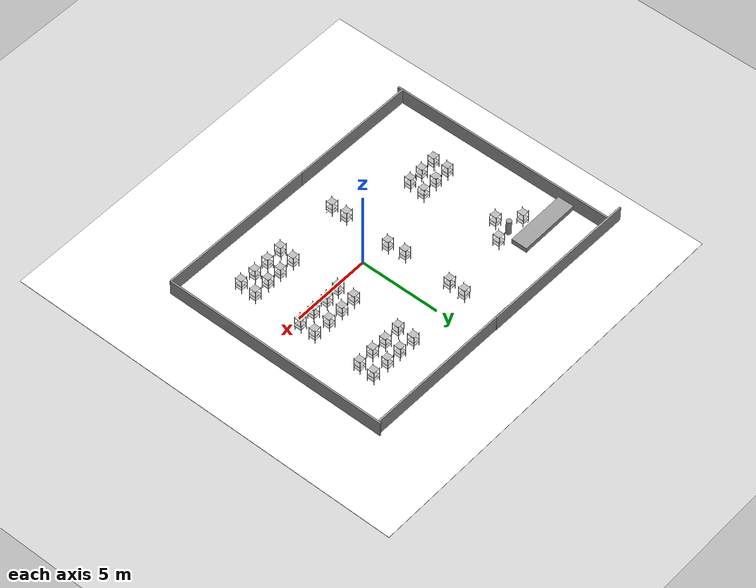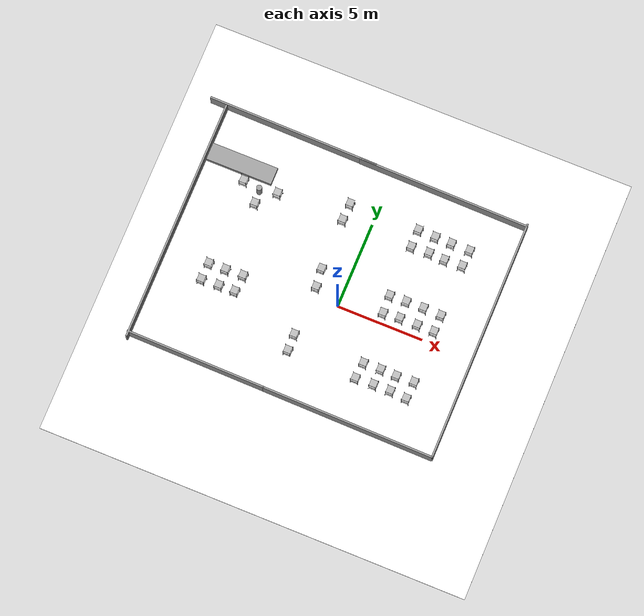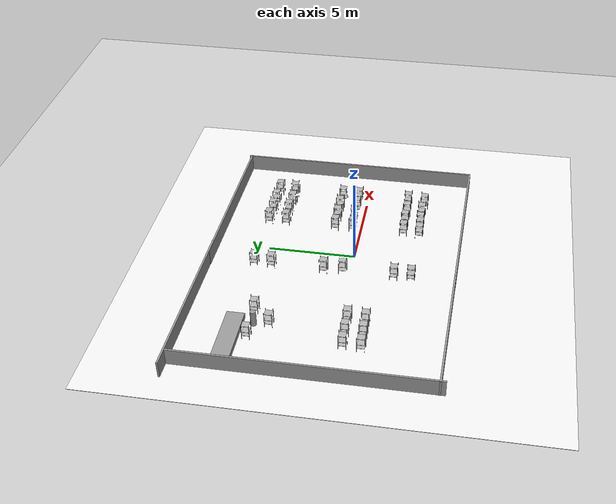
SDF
<sdf version="1.7">
 <world name="default">
  <model name="ground_plane">
   <static>1</static>
   <link name="link">
    <collision name="collision">
     <geometry><plane><normal>0 0 1</normal><size>100 100</size></plane></geometry>
     <surface><friction><ode><mu>100</mu><mu2>50</mu2></ode></friction></surface>
    </collision>
    <visual name="visual">
     <cast_shadows>0</cast_shadows>
     <geometry><plane><normal>0 0 1</normal><size>100 100</size></plane></geometry>
     <material>
      <script><uri>file://media/materials/scripts/gazebo.material</uri><name>Gazebo/Grey</name></script>
     </material>
    </visual>
   </link>
  </model>
  <light name="sun" type="directional">
   <pose>0 0 10 0 -0 0</pose>
   <diffuse>0.8 0.8 0.8 1</diffuse>
   <specular>0.2 0.2 0.2 1</specular>
   <attenuation>
    <range>1000</range>
    <constant>0.9</constant>
    <linear>0.01</linear>
    <quadratic>0.001</quadratic>
   </attenuation>
   <direction>-0.5 0.1 -0.9</direction>
   <spot><inner_angle>0</inner_angle><outer_angle>0</outer_angle><falloff>0</falloff></spot>
  </light>
  <scene><shadows>0</shadows><ambient>0.4 0.4 0.4 1</ambient><background>0.7 0.7 0.7 1</background></scene>
  <physics type="ode">
   <real_time_update_rate>1000</real_time_update_rate>
   <max_step_size>0.001</max_step_size>
   <real_time_factor>1</real_time_factor>
   <ode>
    <solver>
     <type>quick</type>
     <iters>150</iters>
     <precon_iters>0</precon_iters>
     <sor>1.4</sor>
     <use_dynamic_moi_rescaling>1</use_dynamic_moi_rescaling>
    </solver>
    <constraints>
     <cfm>1e-05</cfm>
     <erp>0.2</erp>
     <contact_max_correcting_vel>2000</contact_max_correcting_vel>
     <contact_surface_layer>0.01</contact_surface_layer>
    </constraints>
   </ode>
  </physics>
  <gravity>0 0 -9.8</gravity>
  <magnetic_field>6e-06 2.3e-05 -4.2e-05</magnetic_field>
  <atmosphere type="adiabatic"/>
  <audio><device>default</device></audio>
  <spherical_coordinates>
   <surface_model>EARTH_WGS84</surface_model>
   <latitude_deg>0</latitude_deg>
   <longitude_deg>0</longitude_deg>
   <elevation>0</elevation>
   <heading_deg>0</heading_deg>
  </spherical_coordinates>
  <model name="warehouse_ground">
   <static>1</static>
   <link name="link">
    <pose>0 0 0.01 0 -0 0</pose>
    <collision name="collision">
     <geometry><plane><normal>0 0 1</normal><size>25 25</size></plane></geometry>
     <surface><friction><ode><mu>1</mu><mu2>1</mu2></ode></friction></surface>
    </collision>
    <visual name="visual">
     <geometry><plane><normal>0 0 1</normal><size>25 25</size></plane></geometry>
     <material>
      <ambient>0.95 0.95 0.95 1</ambient>
      <diffuse>0.95 0.95 0.95 1</diffuse>
      <specular>0.1 0.1 0.1 1</specular>
      <emissive>0 0 0 1</emissive>
     </material>
    </visual>
   </link>
  </model>
  <model name="wall_1_clone_clone_clone_0">
   <link name="wall">
    <visual name="visual">
     <geometry><box><size>10 0.1 2</size></box></geometry>
     <material>
      <ambient>0.6 0.6 0.6 1</ambient>
      <shader type="pixel"/>
      <script><name>ModelPreview_1::wall::visual_MATERIAL_</name><uri>__default__</uri></script>
     </material>
    </visual>
    <collision name="collision">
     <geometry><box><size>10 0.1 2</size></box></geometry>
     <surface>
      <friction>
       <ode><mu>1</mu><mu2>1</mu2><fdir1>0 0 0</fdir1><slip1>0</slip1><slip2>0</slip2></ode>
       <torsional>
        <coefficient>1</coefficient>
        <patch_radius>0</patch_radius>
        <surface_radius>0</surface_radius>
        <use_patch_radius>1</use_patch_radius>
        <ode><slip>0</slip></ode>
       </torsional>
      </friction>
      <bounce><restitution_coefficient>0</restitution_coefficient><threshold>1e+06</threshold></bounce>
      <contact>
       <collide_without_contact>0</collide_without_contact>
       <collide_without_contact_bitmask>1</collide_without_contact_bitmask>
       <collide_bitmask>1</collide_bitmask>
       <ode>
        <soft_cfm>0</soft_cfm>
        <soft_erp>0.2</soft_erp>
        <kp>1e+13</kp>
        <kd>1</kd>
        <max_vel>0.01</max_vel>
        <min_depth>0</min_depth>
       </ode>
       <bullet>
        <split_impulse>1</split_impulse>
        <split_impulse_penetration_threshold>-0.01</split_impulse_penetration_threshold>
        <soft_cfm>0</soft_cfm>
        <soft_erp>0.2</soft_erp>
        <kp>1e+13</kp>
        <kd>1</kd>
       </bullet>
      </contact>
     </surface>
    </collision>
   </link>
   <static>1</static>
   <pose>3 -6 0 0 0 -0.012854</pose>
  </model>
  <model name="wall_1_clone_clone_clone_0_clone">
   <link name="wall">
    <visual name="visual">
     <geometry><box><size>14.1649 0.1 2</size></box></geometry>
     <material>
      <ambient>0.6 0.6 0.6 1</ambient>
      <shader type="pixel"/>
      <script><name>ModelPreview_1::wall::visual_MATERIAL_</name><uri>__default__</uri></script>
     </material>
    </visual>
    <collision name="collision">
     <geometry><box><size>14.1649 0.1 2</size></box></geometry>
     <surface>
      <friction>
       <ode><mu>1</mu><mu2>1</mu2><fdir1>0 0 0</fdir1><slip1>0</slip1><slip2>0</slip2></ode>
       <torsional>
        <coefficient>1</coefficient>
        <patch_radius>0</patch_radius>
        <surface_radius>0</surface_radius>
        <use_patch_radius>1</use_patch_radius>
        <ode><slip>0</slip></ode>
       </torsional>
      </friction>
      <bounce><restitution_coefficient>0</restitution_coefficient><threshold>1e+06</threshold></bounce>
      <contact>
       <collide_without_contact>0</collide_without_contact>
       <collide_without_contact_bitmask>1</collide_without_contact_bitmask>
       <collide_bitmask>1</collide_bitmask>
       <ode>
        <soft_cfm>0</soft_cfm>
        <soft_erp>0.2</soft_erp>
        <kp>1e+13</kp>
        <kd>1</kd>
        <max_vel>0.01</max_vel>
        <min_depth>0</min_depth>
       </ode>
       <bullet>
        <split_impulse>1</split_impulse>
        <split_impulse_penetration_threshold>-0.01</split_impulse_penetration_threshold>
        <soft_cfm>0</soft_cfm>
        <soft_erp>0.2</soft_erp>
        <kp>1e+13</kp>
        <kd>1</kd>
       </bullet>
      </contact>
     </surface>
    </collision>
   </link>
   <static>1</static>
   <pose>8 1 0 0 0 -1.5708</pose>
  </model>
  <model name="wall_1_clone_clone_clone_0_clone_0">
   <link name="wall">
    <visual name="visual">
     <geometry><box><size>10 0.1 2</size></box></geometry>
     <material>
      <ambient>0.6 0.6 0.6 1</ambient>
      <shader type="pixel"/>
      <script><name>ModelPreview_1::wall::visual_MATERIAL_</name><uri>__default__</uri></script>
     </material>
    </visual>
    <collision name="collision">
     <geometry><box><size>10 0.1 2</size></box></geometry>
     <surface>
      <friction>
       <ode><mu>1</mu><mu2>1</mu2><fdir1>0 0 0</fdir1><slip1>0</slip1><slip2>0</slip2></ode>
       <torsional>
        <coefficient>1</coefficient>
        <patch_radius>0</patch_radius>
        <surface_radius>0</surface_radius>
        <use_patch_radius>1</use_patch_radius>
        <ode><slip>0</slip></ode>
       </torsional>
      </friction>
      <bounce><restitution_coefficient>0</restitution_coefficient><threshold>1e+06</threshold></bounce>
      <contact>
       <collide_without_contact>0</collide_without_contact>
       <collide_without_contact_bitmask>1</collide_without_contact_bitmask>
       <collide_bitmask>1</collide_bitmask>
       <ode>
        <soft_cfm>0</soft_cfm>
        <soft_erp>0.2</soft_erp>
        <kp>1e+13</kp>
        <kd>1</kd>
        <max_vel>0.01</max_vel>
        <min_depth>0</min_depth>
       </ode>
       <bullet>
        <split_impulse>1</split_impulse>
        <split_impulse_penetration_threshold>-0.01</split_impulse_penetration_threshold>
        <soft_cfm>0</soft_cfm>
        <soft_erp>0.2</soft_erp>
        <kp>1e+13</kp>
        <kd>1</kd>
       </bullet>
      </contact>
     </surface>
    </collision>
   </link>
   <static>1</static>
   <pose>3 8 0 0 0 -0.012854</pose>
  </model>
  <model name="unit_box">
   <pose>-7.98953 5.4744 0.175148 -1.3e-05 -0 1e-05</pose>
   <link name="link">
    <inertial>
     <mass>1</mass>
     <inertia>
      <ixx>0.166667</ixx>
      <ixy>0</ixy>
      <ixz>0</ixz>
      <iyy>0.166667</iyy>
      <iyz>0</iyz>
      <izz>0.166667</izz>
     </inertia>
    </inertial>
    <collision name="collision"><geometry><box><size>3.88925 1 0.330308</size></box></geometry></collision>
    <visual name="visual">
     <geometry><box><size>3.88925 1 0.330308</size></box></geometry>
     <material>
      <script><name>Gazebo/Grey</name><uri>file://media/materials/scripts/gazebo.material</uri></script>
     </material>
    </visual>
   </link>
  </model>
  <model name="unit_cylinder">
   <pose>-6.5019 4.39945 0.480248 0 -0 0</pose>
   <link name="link">
    <inertial>
     <mass>1</mass>
     <inertia><ixx>0.145833</ixx><ixy>0</ixy><ixz>0</ixz><iyy>0.145833</iyy><iyz>0</iyz><izz>0.125</izz></inertia>
    </inertial>
    <collision name="collision">
     <geometry><cylinder><radius>0.160536</radius><length>0.940504</length></cylinder></geometry>
    </collision>
    <visual name="visual">
     <geometry><cylinder><radius>0.160536</radius><length>0.940504</length></cylinder></geometry>
     <material>
      <script><name>Gazebo/Grey</name><uri>file://media/materials/scripts/gazebo.material</uri></script>
     </material>
    </visual>
   </link>
  </model>
  <model name="wall_1_clone_clone_clone_0_clone_0_clone">
   <link name="wall">
    <visual name="visual">
     <geometry><box><size>9.99999 0.1 2</size></box></geometry>
     <material>
      <ambient>0.6 0.6 0.6 1</ambient>
      <shader type="pixel"/>
      <script><name>ModelPreview_1::wall::visual_MATERIAL_</name><uri>__default__</uri></script>
     </material>
    </visual>
    <collision name="collision">
     <geometry><box><size>9.99999 0.1 2</size></box></geometry>
     <surface>
      <friction>
       <ode><mu>1</mu><mu2>1</mu2><fdir1>0 0 0</fdir1><slip1>0</slip1><slip2>0</slip2></ode>
       <torsional>
        <coefficient>1</coefficient>
        <patch_radius>0</patch_radius>
        <surface_radius>0</surface_radius>
        <use_patch_radius>1</use_patch_radius>
        <ode><slip>0</slip></ode>
       </torsional>
      </friction>
      <bounce><restitution_coefficient>0</restitution_coefficient><threshold>1e+06</threshold></bounce>
      <contact>
       <collide_without_contact>0</collide_without_contact>
       <collide_without_contact_bitmask>1</collide_without_contact_bitmask>
       <collide_bitmask>1</collide_bitmask>
       <ode>
        <soft_cfm>0</soft_cfm>
        <soft_erp>0.2</soft_erp>
        <kp>1e+13</kp>
        <kd>1</kd>
        <max_vel>0.01</max_vel>
        <min_depth>0</min_depth>
       </ode>
       <bullet>
        <split_impulse>1</split_impulse>
        <split_impulse_penetration_threshold>-0.01</split_impulse_penetration_threshold>
        <soft_cfm>0</soft_cfm>
        <soft_erp>0.2</soft_erp>
        <kp>1e+13</kp>
        <kd>1</kd>
       </bullet>
      </contact>
     </surface>
    </collision>
   </link>
   <static>1</static>
   <pose>-5.99831 8.13164 0 0 0 -0.012854</pose>
  </model>
  <model name="wall_1_clone_clone_clone_0_clone_clone">
   <link name="wall">
    <visual name="visual">
     <geometry><box><size>14.2546 0.1 2</size></box></geometry>
     <material>
      <ambient>0.6 0.6 0.6 1</ambient>
      <shader type="pixel"/>
      <script><name>ModelPreview_1::wall::visual_MATERIAL_</name><uri>__default__</uri></script>
     </material>
    </visual>
    <collision name="collision">
     <geometry><box><size>14.2546 0.1 2</size></box></geometry>
     <surface>
      <friction>
       <ode><mu>1</mu><mu2>1</mu2><fdir1>0 0 0</fdir1><slip1>0</slip1><slip2>0</slip2></ode>
       <torsional>
        <coefficient>1</coefficient>
        <patch_radius>0</patch_radius>
        <surface_radius>0</surface_radius>
        <use_patch_radius>1</use_patch_radius>
        <ode><slip>0</slip></ode>
       </torsional>
      </friction>
      <bounce><restitution_coefficient>0</restitution_coefficient><threshold>1e+06</threshold></bounce>
      <contact>
       <collide_without_contact>0</collide_without_contact>
       <collide_without_contact_bitmask>1</collide_without_contact_bitmask>
       <collide_bitmask>1</collide_bitmask>
       <ode>
        <soft_cfm>0</soft_cfm>
        <soft_erp>0.2</soft_erp>
        <kp>1e+13</kp>
        <kd>1</kd>
        <max_vel>0.01</max_vel>
        <min_depth>0</min_depth>
       </ode>
       <bullet>
        <split_impulse>1</split_impulse>
        <split_impulse_penetration_threshold>-0.01</split_impulse_penetration_threshold>
        <soft_cfm>0</soft_cfm>
        <soft_erp>0.2</soft_erp>
        <kp>1e+13</kp>
        <kd>1</kd>
       </bullet>
      </contact>
     </surface>
    </collision>
   </link>
   <static>1</static>
   <pose>-10 1 0 0 0 -1.5708</pose>
  </model>
  <model name="wall_1_clone_clone_clone_0_clone_0_clone_clone">
   <link name="wall">
    <visual name="visual">
     <geometry><box><size>8.15726 0.1 2</size></box></geometry>
     <material>
      <ambient>0.6 0.6 0.6 1</ambient>
      <shader type="pixel"/>
      <script><name>ModelPreview_1::wall::visual_MATERIAL_</name><uri>__default__</uri></script>
     </material>
    </visual>
    <collision name="collision">
     <geometry><box><size>8.15726 0.1 2</size></box></geometry>
     <surface>
      <friction>
       <ode><mu>1</mu><mu2>1</mu2><fdir1>0 0 0</fdir1><slip1>0</slip1><slip2>0</slip2></ode>
       <torsional>
        <coefficient>1</coefficient>
        <patch_radius>0</patch_radius>
        <surface_radius>0</surface_radius>
        <use_patch_radius>1</use_patch_radius>
        <ode><slip>0</slip></ode>
       </torsional>
      </friction>
      <bounce><restitution_coefficient>0</restitution_coefficient><threshold>1e+06</threshold></bounce>
      <contact>
       <collide_without_contact>0</collide_without_contact>
       <collide_without_contact_bitmask>1</collide_without_contact_bitmask>
       <collide_bitmask>1</collide_bitmask>
       <ode>
        <soft_cfm>0</soft_cfm>
        <soft_erp>0.2</soft_erp>
        <kp>1e+13</kp>
        <kd>1</kd>
        <max_vel>0.01</max_vel>
        <min_depth>0</min_depth>
       </ode>
       <bullet>
        <split_impulse>1</split_impulse>
        <split_impulse_penetration_threshold>-0.01</split_impulse_penetration_threshold>
        <soft_cfm>0</soft_cfm>
        <soft_erp>0.2</soft_erp>
        <kp>1e+13</kp>
        <kd>1</kd>
       </bullet>
      </contact>
     </surface>
    </collision>
   </link>
   <static>1</static>
   <pose>-5.99845 -5.87929 0 0 0 -0.012854</pose>
  </model>
  <model name="square_shelf_0">
   <link name="link">
    <visual name="bottom_shelf_visual">
     <geometry><box><size>0.4 0.4 0.02</size></box></geometry>
     <pose>0 0 0.25 0 -0 0</pose>
     <material><ambient>0.6 0.6 0.6 1</ambient><diffuse>0.7 0.7 0.7 1</diffuse></material>
    </visual>
    <collision name="bottom_shelf_collision">
     <geometry><box><size>0.4 0.4 0.02</size></box></geometry>
     <pose>0 0 0.25 0 -0 0</pose>
    </collision>
    <visual name="middle_shelf_visual">
     <geometry><box><size>0.4 0.4 0.02</size></box></geometry>
     <pose>0 0 0.5 0 -0 0</pose>
     <material><ambient>0.6 0.6 0.6 1</ambient><diffuse>0.7 0.7 0.7 1</diffuse></material>
    </visual>
    <collision name="middle_shelf_collision">
     <geometry><box><size>0.4 0.4 0.02</size></box></geometry>
     <pose>0 0 0.5 0 -0 0</pose>
    </collision>
    <visual name="top_shelf_visual">
     <geometry><box><size>0.4 0.4 0.02</size></box></geometry>
     <pose>0 0 0.9 0 -0 0</pose>
     <material><ambient>0.6 0.6 0.6 1</ambient><diffuse>0.7 0.7 0.7 1</diffuse></material>
    </visual>
    <collision name="top_shelf_collision">
     <geometry><box><size>0.4 0.4 0.02</size></box></geometry>
     <pose>0 0 0.9 0 -0 0</pose>
    </collision>
    <visual name="left_support_visual">
     <geometry><box><size>0.02 0.02 1</size></box></geometry>
     <pose>-0.21 -0.21 0.5 0 -0 0</pose>
     <material><ambient>0.3 0.3 0.3 1</ambient><diffuse>0.3 0.3 0.3 1</diffuse></material>
    </visual>
    <collision name="left_support_collision">
     <geometry><box><size>0.02 0.02 1</size></box></geometry>
     <pose>-0.21 -0.21 0.5 0 -0 0</pose>
    </collision>
    <visual name="right_support_visual">
     <geometry><box><size>0.02 0.02 1</size></box></geometry>
     <pose>0.21 -0.21 0.5 0 -0 0</pose>
     <material><ambient>0.3 0.3 0.3 1</ambient><diffuse>0.3 0.3 0.3 1</diffuse></material>
    </visual>
    <collision name="right_support_collision">
     <geometry><box><size>0.02 0.02 1</size></box></geometry>
     <pose>0.21 -0.21 0.5 0 -0 0</pose>
    </collision>
    <visual name="front_left_support_visual">
     <geometry><box><size>0.02 0.02 1</size></box></geometry>
     <pose>-0.21 0.21 0.5 0 -0 0</pose>
     <material><ambient>0.3 0.3 0.3 1</ambient><diffuse>0.3 0.3 0.3 1</diffuse></material>
    </visual>
    <collision name="front_left_support_collision">
     <geometry><box><size>0.02 0.02 1</size></box></geometry>
     <pose>-0.21 0.21 0.5 0 -0 0</pose>
    </collision>
    <visual name="front_right_support_visual">
     <geometry><box><size>0.02 0.02 1</size></box></geometry>
     <pose>0.21 0.21 0.5 0 -0 0</pose>
     <material><ambient>0.3 0.3 0.3 1</ambient><diffuse>0.3 0.3 0.3 1</diffuse></material>
    </visual>
    <collision name="front_right_support_collision">
     <geometry><box><size>0.02 0.02 1</size></box></geometry>
     <pose>0.21 0.21 0.5 0 -0 0</pose>
    </collision>
    <inertial>
     <inertia><ixx>1</ixx><ixy>0</ixy><ixz>0</ixz><iyy>1</iyy><iyz>0</iyz><izz>1</izz></inertia>
     <mass>1</mass>
    </inertial>
   </link>
   <pose>-5.46868 4.57634 0.01 -1e-06 1e-06 0</pose>
  </model>
  <model name="square_shelf_0_clone">
   <link name="link">
    <visual name="bottom_shelf_visual">
     <geometry><box><size>0.4 0.4 0.02</size></box></geometry>
     <pose>0 0 0.25 0 -0 0</pose>
     <material><ambient>0.6 0.6 0.6 1</ambient><diffuse>0.7 0.7 0.7 1</diffuse></material>
    </visual>
    <collision name="bottom_shelf_collision">
     <geometry><box><size>0.4 0.4 0.02</size></box></geometry>
     <pose>0 0 0.25 0 -0 0</pose>
    </collision>
    <visual name="middle_shelf_visual">
     <geometry><box><size>0.4 0.4 0.02</size></box></geometry>
     <pose>0 0 0.5 0 -0 0</pose>
     <material><ambient>0.6 0.6 0.6 1</ambient><diffuse>0.7 0.7 0.7 1</diffuse></material>
    </visual>
    <collision name="middle_shelf_collision">
     <geometry><box><size>0.4 0.4 0.02</size></box></geometry>
     <pose>0 0 0.5 0 -0 0</pose>
    </collision>
    <visual name="top_shelf_visual">
     <geometry><box><size>0.4 0.4 0.02</size></box></geometry>
     <pose>0 0 0.9 0 -0 0</pose>
     <material><ambient>0.6 0.6 0.6 1</ambient><diffuse>0.7 0.7 0.7 1</diffuse></material>
    </visual>
    <collision name="top_shelf_collision">
     <geometry><box><size>0.4 0.4 0.02</size></box></geometry>
     <pose>0 0 0.9 0 -0 0</pose>
    </collision>
    <visual name="left_support_visual">
     <geometry><box><size>0.02 0.02 1</size></box></geometry>
     <pose>-0.21 -0.21 0.5 0 -0 0</pose>
     <material><ambient>0.3 0.3 0.3 1</ambient><diffuse>0.3 0.3 0.3 1</diffuse></material>
    </visual>
    <collision name="left_support_collision">
     <geometry><box><size>0.02 0.02 1</size></box></geometry>
     <pose>-0.21 -0.21 0.5 0 -0 0</pose>
    </collision>
    <visual name="right_support_visual">
     <geometry><box><size>0.02 0.02 1</size></box></geometry>
     <pose>0.21 -0.21 0.5 0 -0 0</pose>
     <material><ambient>0.3 0.3 0.3 1</ambient><diffuse>0.3 0.3 0.3 1</diffuse></material>
    </visual>
    <collision name="right_support_collision">
     <geometry><box><size>0.02 0.02 1</size></box></geometry>
     <pose>0.21 -0.21 0.5 0 -0 0</pose>
    </collision>
    <visual name="front_left_support_visual">
     <geometry><box><size>0.02 0.02 1</size></box></geometry>
     <pose>-0.21 0.21 0.5 0 -0 0</pose>
     <material><ambient>0.3 0.3 0.3 1</ambient><diffuse>0.3 0.3 0.3 1</diffuse></material>
    </visual>
    <collision name="front_left_support_collision">
     <geometry><box><size>0.02 0.02 1</size></box></geometry>
     <pose>-0.21 0.21 0.5 0 -0 0</pose>
    </collision>
    <visual name="front_right_support_visual">
     <geometry><box><size>0.02 0.02 1</size></box></geometry>
     <pose>0.21 0.21 0.5 0 -0 0</pose>
     <material><ambient>0.3 0.3 0.3 1</ambient><diffuse>0.3 0.3 0.3 1</diffuse></material>
    </visual>
    <collision name="front_right_support_collision">
     <geometry><box><size>0.02 0.02 1</size></box></geometry>
     <pose>0.21 0.21 0.5 0 -0 0</pose>
    </collision>
    <inertial>
     <inertia><ixx>1</ixx><ixy>0</ixy><ixz>0</ixz><iyy>1</iyy><iyz>0</iyz><izz>1</izz></inertia>
     <mass>1</mass>
    </inertial>
   </link>
   <pose>-6.42039 3.57096 0.01 0 -1e-06 0</pose>
  </model>
  <model name="square_shelf_0_clone_0">
   <link name="link">
    <visual name="bottom_shelf_visual">
     <geometry><box><size>0.4 0.4 0.02</size></box></geometry>
     <pose>0 0 0.25 0 -0 0</pose>
     <material><ambient>0.6 0.6 0.6 1</ambient><diffuse>0.7 0.7 0.7 1</diffuse></material>
    </visual>
    <collision name="bottom_shelf_collision">
     <geometry><box><size>0.4 0.4 0.02</size></box></geometry>
     <pose>0 0 0.25 0 -0 0</pose>
    </collision>
    <visual name="middle_shelf_visual">
     <geometry><box><size>0.4 0.4 0.02</size></box></geometry>
     <pose>0 0 0.5 0 -0 0</pose>
     <material><ambient>0.6 0.6 0.6 1</ambient><diffuse>0.7 0.7 0.7 1</diffuse></material>
    </visual>
    <collision name="middle_shelf_collision">
     <geometry><box><size>0.4 0.4 0.02</size></box></geometry>
     <pose>0 0 0.5 0 -0 0</pose>
    </collision>
    <visual name="top_shelf_visual">
     <geometry><box><size>0.4 0.4 0.02</size></box></geometry>
     <pose>0 0 0.9 0 -0 0</pose>
     <material><ambient>0.6 0.6 0.6 1</ambient><diffuse>0.7 0.7 0.7 1</diffuse></material>
    </visual>
    <collision name="top_shelf_collision">
     <geometry><box><size>0.4 0.4 0.02</size></box></geometry>
     <pose>0 0 0.9 0 -0 0</pose>
    </collision>
    <visual name="left_support_visual">
     <geometry><box><size>0.02 0.02 1</size></box></geometry>
     <pose>-0.21 -0.21 0.5 0 -0 0</pose>
     <material><ambient>0.3 0.3 0.3 1</ambient><diffuse>0.3 0.3 0.3 1</diffuse></material>
    </visual>
    <collision name="left_support_collision">
     <geometry><box><size>0.02 0.02 1</size></box></geometry>
     <pose>-0.21 -0.21 0.5 0 -0 0</pose>
    </collision>
    <visual name="right_support_visual">
     <geometry><box><size>0.02 0.02 1</size></box></geometry>
     <pose>0.21 -0.21 0.5 0 -0 0</pose>
     <material><ambient>0.3 0.3 0.3 1</ambient><diffuse>0.3 0.3 0.3 1</diffuse></material>
    </visual>
    <collision name="right_support_collision">
     <geometry><box><size>0.02 0.02 1</size></box></geometry>
     <pose>0.21 -0.21 0.5 0 -0 0</pose>
    </collision>
    <visual name="front_left_support_visual">
     <geometry><box><size>0.02 0.02 1</size></box></geometry>
     <pose>-0.21 0.21 0.5 0 -0 0</pose>
     <material><ambient>0.3 0.3 0.3 1</ambient><diffuse>0.3 0.3 0.3 1</diffuse></material>
    </visual>
    <collision name="front_left_support_collision">
     <geometry><box><size>0.02 0.02 1</size></box></geometry>
     <pose>-0.21 0.21 0.5 0 -0 0</pose>
    </collision>
    <visual name="front_right_support_visual">
     <geometry><box><size>0.02 0.02 1</size></box></geometry>
     <pose>0.21 0.21 0.5 0 -0 0</pose>
     <material><ambient>0.3 0.3 0.3 1</ambient><diffuse>0.3 0.3 0.3 1</diffuse></material>
    </visual>
    <collision name="front_right_support_collision">
     <geometry><box><size>0.02 0.02 1</size></box></geometry>
     <pose>0.21 0.21 0.5 0 -0 0</pose>
    </collision>
    <inertial>
     <inertia><ixx>1</ixx><ixy>0</ixy><ixz>0</ixz><iyy>1</iyy><iyz>0</iyz><izz>1</izz></inertia>
     <mass>1</mass>
    </inertial>
   </link>
   <pose>-7.48317 4.54339 0.009999 1e-06 -0 0</pose>
  </model>
  <model name="square_shelf_0_clone_1">
   <link name="link">
    <visual name="bottom_shelf_visual">
     <geometry><box><size>0.4 0.4 0.02</size></box></geometry>
     <pose>0 0 0.25 0 -0 0</pose>
     <material><ambient>0.6 0.6 0.6 1</ambient><diffuse>0.7 0.7 0.7 1</diffuse></material>
    </visual>
    <collision name="bottom_shelf_collision">
     <geometry><box><size>0.4 0.4 0.02</size></box></geometry>
     <pose>0 0 0.25 0 -0 0</pose>
    </collision>
    <visual name="middle_shelf_visual">
     <geometry><box><size>0.4 0.4 0.02</size></box></geometry>
     <pose>0 0 0.5 0 -0 0</pose>
     <material><ambient>0.6 0.6 0.6 1</ambient><diffuse>0.7 0.7 0.7 1</diffuse></material>
    </visual>
    <collision name="middle_shelf_collision">
     <geometry><box><size>0.4 0.4 0.02</size></box></geometry>
     <pose>0 0 0.5 0 -0 0</pose>
    </collision>
    <visual name="top_shelf_visual">
     <geometry><box><size>0.4 0.4 0.02</size></box></geometry>
     <pose>0 0 0.9 0 -0 0</pose>
     <material><ambient>0.6 0.6 0.6 1</ambient><diffuse>0.7 0.7 0.7 1</diffuse></material>
    </visual>
    <collision name="top_shelf_collision">
     <geometry><box><size>0.4 0.4 0.02</size></box></geometry>
     <pose>0 0 0.9 0 -0 0</pose>
    </collision>
    <visual name="left_support_visual">
     <geometry><box><size>0.02 0.02 1</size></box></geometry>
     <pose>-0.21 -0.21 0.5 0 -0 0</pose>
     <material><ambient>0.3 0.3 0.3 1</ambient><diffuse>0.3 0.3 0.3 1</diffuse></material>
    </visual>
    <collision name="left_support_collision">
     <geometry><box><size>0.02 0.02 1</size></box></geometry>
     <pose>-0.21 -0.21 0.5 0 -0 0</pose>
    </collision>
    <visual name="right_support_visual">
     <geometry><box><size>0.02 0.02 1</size></box></geometry>
     <pose>0.21 -0.21 0.5 0 -0 0</pose>
     <material><ambient>0.3 0.3 0.3 1</ambient><diffuse>0.3 0.3 0.3 1</diffuse></material>
    </visual>
    <collision name="right_support_collision">
     <geometry><box><size>0.02 0.02 1</size></box></geometry>
     <pose>0.21 -0.21 0.5 0 -0 0</pose>
    </collision>
    <visual name="front_left_support_visual">
     <geometry><box><size>0.02 0.02 1</size></box></geometry>
     <pose>-0.21 0.21 0.5 0 -0 0</pose>
     <material><ambient>0.3 0.3 0.3 1</ambient><diffuse>0.3 0.3 0.3 1</diffuse></material>
    </visual>
    <collision name="front_left_support_collision">
     <geometry><box><size>0.02 0.02 1</size></box></geometry>
     <pose>-0.21 0.21 0.5 0 -0 0</pose>
    </collision>
    <visual name="front_right_support_visual">
     <geometry><box><size>0.02 0.02 1</size></box></geometry>
     <pose>0.21 0.21 0.5 0 -0 0</pose>
     <material><ambient>0.3 0.3 0.3 1</ambient><diffuse>0.3 0.3 0.3 1</diffuse></material>
    </visual>
    <collision name="front_right_support_collision">
     <geometry><box><size>0.02 0.02 1</size></box></geometry>
     <pose>0.21 0.21 0.5 0 -0 0</pose>
    </collision>
    <inertial>
     <inertia><ixx>1</ixx><ixy>0</ixy><ixz>0</ixz><iyy>1</iyy><iyz>0</iyz><izz>1</izz></inertia>
     <mass>1</mass>
    </inertial>
   </link>
   <pose>-5.43919 -0.483465 0.01 0 -1e-06 0</pose>
  </model>
  <model name="square_shelf_0_clone_2">
   <link name="link">
    <visual name="bottom_shelf_visual">
     <geometry><box><size>0.4 0.4 0.02</size></box></geometry>
     <pose>0 0 0.25 0 -0 0</pose>
     <material><ambient>0.6 0.6 0.6 1</ambient><diffuse>0.7 0.7 0.7 1</diffuse></material>
    </visual>
    <collision name="bottom_shelf_collision">
     <geometry><box><size>0.4 0.4 0.02</size></box></geometry>
     <pose>0 0 0.25 0 -0 0</pose>
    </collision>
    <visual name="middle_shelf_visual">
     <geometry><box><size>0.4 0.4 0.02</size></box></geometry>
     <pose>0 0 0.5 0 -0 0</pose>
     <material><ambient>0.6 0.6 0.6 1</ambient><diffuse>0.7 0.7 0.7 1</diffuse></material>
    </visual>
    <collision name="middle_shelf_collision">
     <geometry><box><size>0.4 0.4 0.02</size></box></geometry>
     <pose>0 0 0.5 0 -0 0</pose>
    </collision>
    <visual name="top_shelf_visual">
     <geometry><box><size>0.4 0.4 0.02</size></box></geometry>
     <pose>0 0 0.9 0 -0 0</pose>
     <material><ambient>0.6 0.6 0.6 1</ambient><diffuse>0.7 0.7 0.7 1</diffuse></material>
    </visual>
    <collision name="top_shelf_collision">
     <geometry><box><size>0.4 0.4 0.02</size></box></geometry>
     <pose>0 0 0.9 0 -0 0</pose>
    </collision>
    <visual name="left_support_visual">
     <geometry><box><size>0.02 0.02 1</size></box></geometry>
     <pose>-0.21 -0.21 0.5 0 -0 0</pose>
     <material><ambient>0.3 0.3 0.3 1</ambient><diffuse>0.3 0.3 0.3 1</diffuse></material>
    </visual>
    <collision name="left_support_collision">
     <geometry><box><size>0.02 0.02 1</size></box></geometry>
     <pose>-0.21 -0.21 0.5 0 -0 0</pose>
    </collision>
    <visual name="right_support_visual">
     <geometry><box><size>0.02 0.02 1</size></box></geometry>
     <pose>0.21 -0.21 0.5 0 -0 0</pose>
     <material><ambient>0.3 0.3 0.3 1</ambient><diffuse>0.3 0.3 0.3 1</diffuse></material>
    </visual>
    <collision name="right_support_collision">
     <geometry><box><size>0.02 0.02 1</size></box></geometry>
     <pose>0.21 -0.21 0.5 0 -0 0</pose>
    </collision>
    <visual name="front_left_support_visual">
     <geometry><box><size>0.02 0.02 1</size></box></geometry>
     <pose>-0.21 0.21 0.5 0 -0 0</pose>
     <material><ambient>0.3 0.3 0.3 1</ambient><diffuse>0.3 0.3 0.3 1</diffuse></material>
    </visual>
    <collision name="front_left_support_collision">
     <geometry><box><size>0.02 0.02 1</size></box></geometry>
     <pose>-0.21 0.21 0.5 0 -0 0</pose>
    </collision>
    <visual name="front_right_support_visual">
     <geometry><box><size>0.02 0.02 1</size></box></geometry>
     <pose>0.21 0.21 0.5 0 -0 0</pose>
     <material><ambient>0.3 0.3 0.3 1</ambient><diffuse>0.3 0.3 0.3 1</diffuse></material>
    </visual>
    <collision name="front_right_support_collision">
     <geometry><box><size>0.02 0.02 1</size></box></geometry>
     <pose>0.21 0.21 0.5 0 -0 0</pose>
    </collision>
    <inertial>
     <inertia><ixx>1</ixx><ixy>0</ixy><ixz>0</ixz><iyy>1</iyy><iyz>0</iyz><izz>1</izz></inertia>
     <mass>1</mass>
    </inertial>
   </link>
   <pose>-6.46501 -0.524736 0.009991 -1e-06 -0 0</pose>
  </model>
  <model name="square_shelf_0_clone_3">
   <link name="link">
    <visual name="bottom_shelf_visual">
     <geometry><box><size>0.4 0.4 0.02</size></box></geometry>
     <pose>0 0 0.25 0 -0 0</pose>
     <material><ambient>0.6 0.6 0.6 1</ambient><diffuse>0.7 0.7 0.7 1</diffuse></material>
    </visual>
    <collision name="bottom_shelf_collision">
     <geometry><box><size>0.4 0.4 0.02</size></box></geometry>
     <pose>0 0 0.25 0 -0 0</pose>
    </collision>
    <visual name="middle_shelf_visual">
     <geometry><box><size>0.4 0.4 0.02</size></box></geometry>
     <pose>0 0 0.5 0 -0 0</pose>
     <material><ambient>0.6 0.6 0.6 1</ambient><diffuse>0.7 0.7 0.7 1</diffuse></material>
    </visual>
    <collision name="middle_shelf_collision">
     <geometry><box><size>0.4 0.4 0.02</size></box></geometry>
     <pose>0 0 0.5 0 -0 0</pose>
    </collision>
    <visual name="top_shelf_visual">
     <geometry><box><size>0.4 0.4 0.02</size></box></geometry>
     <pose>0 0 0.9 0 -0 0</pose>
     <material><ambient>0.6 0.6 0.6 1</ambient><diffuse>0.7 0.7 0.7 1</diffuse></material>
    </visual>
    <collision name="top_shelf_collision">
     <geometry><box><size>0.4 0.4 0.02</size></box></geometry>
     <pose>0 0 0.9 0 -0 0</pose>
    </collision>
    <visual name="left_support_visual">
     <geometry><box><size>0.02 0.02 1</size></box></geometry>
     <pose>-0.21 -0.21 0.5 0 -0 0</pose>
     <material><ambient>0.3 0.3 0.3 1</ambient><diffuse>0.3 0.3 0.3 1</diffuse></material>
    </visual>
    <collision name="left_support_collision">
     <geometry><box><size>0.02 0.02 1</size></box></geometry>
     <pose>-0.21 -0.21 0.5 0 -0 0</pose>
    </collision>
    <visual name="right_support_visual">
     <geometry><box><size>0.02 0.02 1</size></box></geometry>
     <pose>0.21 -0.21 0.5 0 -0 0</pose>
     <material><ambient>0.3 0.3 0.3 1</ambient><diffuse>0.3 0.3 0.3 1</diffuse></material>
    </visual>
    <collision name="right_support_collision">
     <geometry><box><size>0.02 0.02 1</size></box></geometry>
     <pose>0.21 -0.21 0.5 0 -0 0</pose>
    </collision>
    <visual name="front_left_support_visual">
     <geometry><box><size>0.02 0.02 1</size></box></geometry>
     <pose>-0.21 0.21 0.5 0 -0 0</pose>
     <material><ambient>0.3 0.3 0.3 1</ambient><diffuse>0.3 0.3 0.3 1</diffuse></material>
    </visual>
    <collision name="front_left_support_collision">
     <geometry><box><size>0.02 0.02 1</size></box></geometry>
     <pose>-0.21 0.21 0.5 0 -0 0</pose>
    </collision>
    <visual name="front_right_support_visual">
     <geometry><box><size>0.02 0.02 1</size></box></geometry>
     <pose>0.21 0.21 0.5 0 -0 0</pose>
     <material><ambient>0.3 0.3 0.3 1</ambient><diffuse>0.3 0.3 0.3 1</diffuse></material>
    </visual>
    <collision name="front_right_support_collision">
     <geometry><box><size>0.02 0.02 1</size></box></geometry>
     <pose>0.21 0.21 0.5 0 -0 0</pose>
    </collision>
    <inertial>
     <inertia><ixx>1</ixx><ixy>0</ixy><ixz>0</ixz><iyy>1</iyy><iyz>0</iyz><izz>1</izz></inertia>
     <mass>1</mass>
    </inertial>
   </link>
   <pose>-7.44564 -0.553046 0.009999 1e-06 -0 0</pose>
  </model>
  <model name="square_shelf_0_clone_4">
   <link name="link">
    <visual name="bottom_shelf_visual">
     <geometry><box><size>0.4 0.4 0.02</size></box></geometry>
     <pose>0 0 0.25 0 -0 0</pose>
     <material><ambient>0.6 0.6 0.6 1</ambient><diffuse>0.7 0.7 0.7 1</diffuse></material>
    </visual>
    <collision name="bottom_shelf_collision">
     <geometry><box><size>0.4 0.4 0.02</size></box></geometry>
     <pose>0 0 0.25 0 -0 0</pose>
    </collision>
    <visual name="middle_shelf_visual">
     <geometry><box><size>0.4 0.4 0.02</size></box></geometry>
     <pose>0 0 0.5 0 -0 0</pose>
     <material><ambient>0.6 0.6 0.6 1</ambient><diffuse>0.7 0.7 0.7 1</diffuse></material>
    </visual>
    <collision name="middle_shelf_collision">
     <geometry><box><size>0.4 0.4 0.02</size></box></geometry>
     <pose>0 0 0.5 0 -0 0</pose>
    </collision>
    <visual name="top_shelf_visual">
     <geometry><box><size>0.4 0.4 0.02</size></box></geometry>
     <pose>0 0 0.9 0 -0 0</pose>
     <material><ambient>0.6 0.6 0.6 1</ambient><diffuse>0.7 0.7 0.7 1</diffuse></material>
    </visual>
    <collision name="top_shelf_collision">
     <geometry><box><size>0.4 0.4 0.02</size></box></geometry>
     <pose>0 0 0.9 0 -0 0</pose>
    </collision>
    <visual name="left_support_visual">
     <geometry><box><size>0.02 0.02 1</size></box></geometry>
     <pose>-0.21 -0.21 0.5 0 -0 0</pose>
     <material><ambient>0.3 0.3 0.3 1</ambient><diffuse>0.3 0.3 0.3 1</diffuse></material>
    </visual>
    <collision name="left_support_collision">
     <geometry><box><size>0.02 0.02 1</size></box></geometry>
     <pose>-0.21 -0.21 0.5 0 -0 0</pose>
    </collision>
    <visual name="right_support_visual">
     <geometry><box><size>0.02 0.02 1</size></box></geometry>
     <pose>0.21 -0.21 0.5 0 -0 0</pose>
     <material><ambient>0.3 0.3 0.3 1</ambient><diffuse>0.3 0.3 0.3 1</diffuse></material>
    </visual>
    <collision name="right_support_collision">
     <geometry><box><size>0.02 0.02 1</size></box></geometry>
     <pose>0.21 -0.21 0.5 0 -0 0</pose>
    </collision>
    <visual name="front_left_support_visual">
     <geometry><box><size>0.02 0.02 1</size></box></geometry>
     <pose>-0.21 0.21 0.5 0 -0 0</pose>
     <material><ambient>0.3 0.3 0.3 1</ambient><diffuse>0.3 0.3 0.3 1</diffuse></material>
    </visual>
    <collision name="front_left_support_collision">
     <geometry><box><size>0.02 0.02 1</size></box></geometry>
     <pose>-0.21 0.21 0.5 0 -0 0</pose>
    </collision>
    <visual name="front_right_support_visual">
     <geometry><box><size>0.02 0.02 1</size></box></geometry>
     <pose>0.21 0.21 0.5 0 -0 0</pose>
     <material><ambient>0.3 0.3 0.3 1</ambient><diffuse>0.3 0.3 0.3 1</diffuse></material>
    </visual>
    <collision name="front_right_support_collision">
     <geometry><box><size>0.02 0.02 1</size></box></geometry>
     <pose>0.21 0.21 0.5 0 -0 0</pose>
    </collision>
    <inertial>
     <inertia><ixx>1</ixx><ixy>0</ixy><ixz>0</ixz><iyy>1</iyy><iyz>0</iyz><izz>1</izz></inertia>
     <mass>1</mass>
    </inertial>
   </link>
   <pose>-7.48409 -1.5373 0.009999 1e-06 -0 0</pose>
  </model>
  <model name="square_shelf_0_clone_5">
   <link name="link">
    <visual name="bottom_shelf_visual">
     <geometry><box><size>0.4 0.4 0.02</size></box></geometry>
     <pose>0 0 0.25 0 -0 0</pose>
     <material><ambient>0.6 0.6 0.6 1</ambient><diffuse>0.7 0.7 0.7 1</diffuse></material>
    </visual>
    <collision name="bottom_shelf_collision">
     <geometry><box><size>0.4 0.4 0.02</size></box></geometry>
     <pose>0 0 0.25 0 -0 0</pose>
    </collision>
    <visual name="middle_shelf_visual">
     <geometry><box><size>0.4 0.4 0.02</size></box></geometry>
     <pose>0 0 0.5 0 -0 0</pose>
     <material><ambient>0.6 0.6 0.6 1</ambient><diffuse>0.7 0.7 0.7 1</diffuse></material>
    </visual>
    <collision name="middle_shelf_collision">
     <geometry><box><size>0.4 0.4 0.02</size></box></geometry>
     <pose>0 0 0.5 0 -0 0</pose>
    </collision>
    <visual name="top_shelf_visual">
     <geometry><box><size>0.4 0.4 0.02</size></box></geometry>
     <pose>0 0 0.9 0 -0 0</pose>
     <material><ambient>0.6 0.6 0.6 1</ambient><diffuse>0.7 0.7 0.7 1</diffuse></material>
    </visual>
    <collision name="top_shelf_collision">
     <geometry><box><size>0.4 0.4 0.02</size></box></geometry>
     <pose>0 0 0.9 0 -0 0</pose>
    </collision>
    <visual name="left_support_visual">
     <geometry><box><size>0.02 0.02 1</size></box></geometry>
     <pose>-0.21 -0.21 0.5 0 -0 0</pose>
     <material><ambient>0.3 0.3 0.3 1</ambient><diffuse>0.3 0.3 0.3 1</diffuse></material>
    </visual>
    <collision name="left_support_collision">
     <geometry><box><size>0.02 0.02 1</size></box></geometry>
     <pose>-0.21 -0.21 0.5 0 -0 0</pose>
    </collision>
    <visual name="right_support_visual">
     <geometry><box><size>0.02 0.02 1</size></box></geometry>
     <pose>0.21 -0.21 0.5 0 -0 0</pose>
     <material><ambient>0.3 0.3 0.3 1</ambient><diffuse>0.3 0.3 0.3 1</diffuse></material>
    </visual>
    <collision name="right_support_collision">
     <geometry><box><size>0.02 0.02 1</size></box></geometry>
     <pose>0.21 -0.21 0.5 0 -0 0</pose>
    </collision>
    <visual name="front_left_support_visual">
     <geometry><box><size>0.02 0.02 1</size></box></geometry>
     <pose>-0.21 0.21 0.5 0 -0 0</pose>
     <material><ambient>0.3 0.3 0.3 1</ambient><diffuse>0.3 0.3 0.3 1</diffuse></material>
    </visual>
    <collision name="front_left_support_collision">
     <geometry><box><size>0.02 0.02 1</size></box></geometry>
     <pose>-0.21 0.21 0.5 0 -0 0</pose>
    </collision>
    <visual name="front_right_support_visual">
     <geometry><box><size>0.02 0.02 1</size></box></geometry>
     <pose>0.21 0.21 0.5 0 -0 0</pose>
     <material><ambient>0.3 0.3 0.3 1</ambient><diffuse>0.3 0.3 0.3 1</diffuse></material>
    </visual>
    <collision name="front_right_support_collision">
     <geometry><box><size>0.02 0.02 1</size></box></geometry>
     <pose>0.21 0.21 0.5 0 -0 0</pose>
    </collision>
    <inertial>
     <inertia><ixx>1</ixx><ixy>0</ixy><ixz>0</ixz><iyy>1</iyy><iyz>0</iyz><izz>1</izz></inertia>
     <mass>1</mass>
    </inertial>
   </link>
   <pose>-6.45954 -1.49627 0.009999 1e-06 -0 0</pose>
  </model>
  <model name="square_shelf_0_clone_6">
   <link name="link">
    <visual name="bottom_shelf_visual">
     <geometry><box><size>0.4 0.4 0.02</size></box></geometry>
     <pose>0 0 0.25 0 -0 0</pose>
     <material><ambient>0.6 0.6 0.6 1</ambient><diffuse>0.7 0.7 0.7 1</diffuse></material>
    </visual>
    <collision name="bottom_shelf_collision">
     <geometry><box><size>0.4 0.4 0.02</size></box></geometry>
     <pose>0 0 0.25 0 -0 0</pose>
    </collision>
    <visual name="middle_shelf_visual">
     <geometry><box><size>0.4 0.4 0.02</size></box></geometry>
     <pose>0 0 0.5 0 -0 0</pose>
     <material><ambient>0.6 0.6 0.6 1</ambient><diffuse>0.7 0.7 0.7 1</diffuse></material>
    </visual>
    <collision name="middle_shelf_collision">
     <geometry><box><size>0.4 0.4 0.02</size></box></geometry>
     <pose>0 0 0.5 0 -0 0</pose>
    </collision>
    <visual name="top_shelf_visual">
     <geometry><box><size>0.4 0.4 0.02</size></box></geometry>
     <pose>0 0 0.9 0 -0 0</pose>
     <material><ambient>0.6 0.6 0.6 1</ambient><diffuse>0.7 0.7 0.7 1</diffuse></material>
    </visual>
    <collision name="top_shelf_collision">
     <geometry><box><size>0.4 0.4 0.02</size></box></geometry>
     <pose>0 0 0.9 0 -0 0</pose>
    </collision>
    <visual name="left_support_visual">
     <geometry><box><size>0.02 0.02 1</size></box></geometry>
     <pose>-0.21 -0.21 0.5 0 -0 0</pose>
     <material><ambient>0.3 0.3 0.3 1</ambient><diffuse>0.3 0.3 0.3 1</diffuse></material>
    </visual>
    <collision name="left_support_collision">
     <geometry><box><size>0.02 0.02 1</size></box></geometry>
     <pose>-0.21 -0.21 0.5 0 -0 0</pose>
    </collision>
    <visual name="right_support_visual">
     <geometry><box><size>0.02 0.02 1</size></box></geometry>
     <pose>0.21 -0.21 0.5 0 -0 0</pose>
     <material><ambient>0.3 0.3 0.3 1</ambient><diffuse>0.3 0.3 0.3 1</diffuse></material>
    </visual>
    <collision name="right_support_collision">
     <geometry><box><size>0.02 0.02 1</size></box></geometry>
     <pose>0.21 -0.21 0.5 0 -0 0</pose>
    </collision>
    <visual name="front_left_support_visual">
     <geometry><box><size>0.02 0.02 1</size></box></geometry>
     <pose>-0.21 0.21 0.5 0 -0 0</pose>
     <material><ambient>0.3 0.3 0.3 1</ambient><diffuse>0.3 0.3 0.3 1</diffuse></material>
    </visual>
    <collision name="front_left_support_collision">
     <geometry><box><size>0.02 0.02 1</size></box></geometry>
     <pose>-0.21 0.21 0.5 0 -0 0</pose>
    </collision>
    <visual name="front_right_support_visual">
     <geometry><box><size>0.02 0.02 1</size></box></geometry>
     <pose>0.21 0.21 0.5 0 -0 0</pose>
     <material><ambient>0.3 0.3 0.3 1</ambient><diffuse>0.3 0.3 0.3 1</diffuse></material>
    </visual>
    <collision name="front_right_support_collision">
     <geometry><box><size>0.02 0.02 1</size></box></geometry>
     <pose>0.21 0.21 0.5 0 -0 0</pose>
    </collision>
    <inertial>
     <inertia><ixx>1</ixx><ixy>0</ixy><ixz>0</ixz><iyy>1</iyy><iyz>0</iyz><izz>1</izz></inertia>
     <mass>1</mass>
    </inertial>
   </link>
   <pose>-5.52099 -1.47764 0.009999 1e-06 -0 0</pose>
  </model>
  <model name="square_shelf_0_clone_7">
   <link name="link">
    <visual name="bottom_shelf_visual">
     <geometry><box><size>0.4 0.4 0.02</size></box></geometry>
     <pose>0 0 0.25 0 -0 0</pose>
     <material><ambient>0.6 0.6 0.6 1</ambient><diffuse>0.7 0.7 0.7 1</diffuse></material>
    </visual>
    <collision name="bottom_shelf_collision">
     <geometry><box><size>0.4 0.4 0.02</size></box></geometry>
     <pose>0 0 0.25 0 -0 0</pose>
    </collision>
    <visual name="middle_shelf_visual">
     <geometry><box><size>0.4 0.4 0.02</size></box></geometry>
     <pose>0 0 0.5 0 -0 0</pose>
     <material><ambient>0.6 0.6 0.6 1</ambient><diffuse>0.7 0.7 0.7 1</diffuse></material>
    </visual>
    <collision name="middle_shelf_collision">
     <geometry><box><size>0.4 0.4 0.02</size></box></geometry>
     <pose>0 0 0.5 0 -0 0</pose>
    </collision>
    <visual name="top_shelf_visual">
     <geometry><box><size>0.4 0.4 0.02</size></box></geometry>
     <pose>0 0 0.9 0 -0 0</pose>
     <material><ambient>0.6 0.6 0.6 1</ambient><diffuse>0.7 0.7 0.7 1</diffuse></material>
    </visual>
    <collision name="top_shelf_collision">
     <geometry><box><size>0.4 0.4 0.02</size></box></geometry>
     <pose>0 0 0.9 0 -0 0</pose>
    </collision>
    <visual name="left_support_visual">
     <geometry><box><size>0.02 0.02 1</size></box></geometry>
     <pose>-0.21 -0.21 0.5 0 -0 0</pose>
     <material><ambient>0.3 0.3 0.3 1</ambient><diffuse>0.3 0.3 0.3 1</diffuse></material>
    </visual>
    <collision name="left_support_collision">
     <geometry><box><size>0.02 0.02 1</size></box></geometry>
     <pose>-0.21 -0.21 0.5 0 -0 0</pose>
    </collision>
    <visual name="right_support_visual">
     <geometry><box><size>0.02 0.02 1</size></box></geometry>
     <pose>0.21 -0.21 0.5 0 -0 0</pose>
     <material><ambient>0.3 0.3 0.3 1</ambient><diffuse>0.3 0.3 0.3 1</diffuse></material>
    </visual>
    <collision name="right_support_collision">
     <geometry><box><size>0.02 0.02 1</size></box></geometry>
     <pose>0.21 -0.21 0.5 0 -0 0</pose>
    </collision>
    <visual name="front_left_support_visual">
     <geometry><box><size>0.02 0.02 1</size></box></geometry>
     <pose>-0.21 0.21 0.5 0 -0 0</pose>
     <material><ambient>0.3 0.3 0.3 1</ambient><diffuse>0.3 0.3 0.3 1</diffuse></material>
    </visual>
    <collision name="front_left_support_collision">
     <geometry><box><size>0.02 0.02 1</size></box></geometry>
     <pose>-0.21 0.21 0.5 0 -0 0</pose>
    </collision>
    <visual name="front_right_support_visual">
     <geometry><box><size>0.02 0.02 1</size></box></geometry>
     <pose>0.21 0.21 0.5 0 -0 0</pose>
     <material><ambient>0.3 0.3 0.3 1</ambient><diffuse>0.3 0.3 0.3 1</diffuse></material>
    </visual>
    <collision name="front_right_support_collision">
     <geometry><box><size>0.02 0.02 1</size></box></geometry>
     <pose>0.21 0.21 0.5 0 -0 0</pose>
    </collision>
    <inertial>
     <inertia><ixx>1</ixx><ixy>0</ixy><ixz>0</ixz><iyy>1</iyy><iyz>0</iyz><izz>1</izz></inertia>
     <mass>1</mass>
    </inertial>
   </link>
   <pose>-1.52316 5.53311 0.01 0 -0 0</pose>
  </model>
  <model name="square_shelf_0_clone_8">
   <link name="link">
    <visual name="bottom_shelf_visual">
     <geometry><box><size>0.4 0.4 0.02</size></box></geometry>
     <pose>0 0 0.25 0 -0 0</pose>
     <material><ambient>0.6 0.6 0.6 1</ambient><diffuse>0.7 0.7 0.7 1</diffuse></material>
    </visual>
    <collision name="bottom_shelf_collision">
     <geometry><box><size>0.4 0.4 0.02</size></box></geometry>
     <pose>0 0 0.25 0 -0 0</pose>
    </collision>
    <visual name="middle_shelf_visual">
     <geometry><box><size>0.4 0.4 0.02</size></box></geometry>
     <pose>0 0 0.5 0 -0 0</pose>
     <material><ambient>0.6 0.6 0.6 1</ambient><diffuse>0.7 0.7 0.7 1</diffuse></material>
    </visual>
    <collision name="middle_shelf_collision">
     <geometry><box><size>0.4 0.4 0.02</size></box></geometry>
     <pose>0 0 0.5 0 -0 0</pose>
    </collision>
    <visual name="top_shelf_visual">
     <geometry><box><size>0.4 0.4 0.02</size></box></geometry>
     <pose>0 0 0.9 0 -0 0</pose>
     <material><ambient>0.6 0.6 0.6 1</ambient><diffuse>0.7 0.7 0.7 1</diffuse></material>
    </visual>
    <collision name="top_shelf_collision">
     <geometry><box><size>0.4 0.4 0.02</size></box></geometry>
     <pose>0 0 0.9 0 -0 0</pose>
    </collision>
    <visual name="left_support_visual">
     <geometry><box><size>0.02 0.02 1</size></box></geometry>
     <pose>-0.21 -0.21 0.5 0 -0 0</pose>
     <material><ambient>0.3 0.3 0.3 1</ambient><diffuse>0.3 0.3 0.3 1</diffuse></material>
    </visual>
    <collision name="left_support_collision">
     <geometry><box><size>0.02 0.02 1</size></box></geometry>
     <pose>-0.21 -0.21 0.5 0 -0 0</pose>
    </collision>
    <visual name="right_support_visual">
     <geometry><box><size>0.02 0.02 1</size></box></geometry>
     <pose>0.21 -0.21 0.5 0 -0 0</pose>
     <material><ambient>0.3 0.3 0.3 1</ambient><diffuse>0.3 0.3 0.3 1</diffuse></material>
    </visual>
    <collision name="right_support_collision">
     <geometry><box><size>0.02 0.02 1</size></box></geometry>
     <pose>0.21 -0.21 0.5 0 -0 0</pose>
    </collision>
    <visual name="front_left_support_visual">
     <geometry><box><size>0.02 0.02 1</size></box></geometry>
     <pose>-0.21 0.21 0.5 0 -0 0</pose>
     <material><ambient>0.3 0.3 0.3 1</ambient><diffuse>0.3 0.3 0.3 1</diffuse></material>
    </visual>
    <collision name="front_left_support_collision">
     <geometry><box><size>0.02 0.02 1</size></box></geometry>
     <pose>-0.21 0.21 0.5 0 -0 0</pose>
    </collision>
    <visual name="front_right_support_visual">
     <geometry><box><size>0.02 0.02 1</size></box></geometry>
     <pose>0.21 0.21 0.5 0 -0 0</pose>
     <material><ambient>0.3 0.3 0.3 1</ambient><diffuse>0.3 0.3 0.3 1</diffuse></material>
    </visual>
    <collision name="front_right_support_collision">
     <geometry><box><size>0.02 0.02 1</size></box></geometry>
     <pose>0.21 0.21 0.5 0 -0 0</pose>
    </collision>
    <inertial>
     <inertia><ixx>1</ixx><ixy>0</ixy><ixz>0</ixz><iyy>1</iyy><iyz>0</iyz><izz>1</izz></inertia>
     <mass>1</mass>
    </inertial>
   </link>
   <pose>-1.56464 4.52839 0.009999 1e-06 -0 0</pose>
  </model>
  <model name="square_shelf_0_clone_9">
   <link name="link">
    <visual name="bottom_shelf_visual">
     <geometry><box><size>0.4 0.4 0.02</size></box></geometry>
     <pose>0 0 0.25 0 -0 0</pose>
     <material><ambient>0.6 0.6 0.6 1</ambient><diffuse>0.7 0.7 0.7 1</diffuse></material>
    </visual>
    <collision name="bottom_shelf_collision">
     <geometry><box><size>0.4 0.4 0.02</size></box></geometry>
     <pose>0 0 0.25 0 -0 0</pose>
    </collision>
    <visual name="middle_shelf_visual">
     <geometry><box><size>0.4 0.4 0.02</size></box></geometry>
     <pose>0 0 0.5 0 -0 0</pose>
     <material><ambient>0.6 0.6 0.6 1</ambient><diffuse>0.7 0.7 0.7 1</diffuse></material>
    </visual>
    <collision name="middle_shelf_collision">
     <geometry><box><size>0.4 0.4 0.02</size></box></geometry>
     <pose>0 0 0.5 0 -0 0</pose>
    </collision>
    <visual name="top_shelf_visual">
     <geometry><box><size>0.4 0.4 0.02</size></box></geometry>
     <pose>0 0 0.9 0 -0 0</pose>
     <material><ambient>0.6 0.6 0.6 1</ambient><diffuse>0.7 0.7 0.7 1</diffuse></material>
    </visual>
    <collision name="top_shelf_collision">
     <geometry><box><size>0.4 0.4 0.02</size></box></geometry>
     <pose>0 0 0.9 0 -0 0</pose>
    </collision>
    <visual name="left_support_visual">
     <geometry><box><size>0.02 0.02 1</size></box></geometry>
     <pose>-0.21 -0.21 0.5 0 -0 0</pose>
     <material><ambient>0.3 0.3 0.3 1</ambient><diffuse>0.3 0.3 0.3 1</diffuse></material>
    </visual>
    <collision name="left_support_collision">
     <geometry><box><size>0.02 0.02 1</size></box></geometry>
     <pose>-0.21 -0.21 0.5 0 -0 0</pose>
    </collision>
    <visual name="right_support_visual">
     <geometry><box><size>0.02 0.02 1</size></box></geometry>
     <pose>0.21 -0.21 0.5 0 -0 0</pose>
     <material><ambient>0.3 0.3 0.3 1</ambient><diffuse>0.3 0.3 0.3 1</diffuse></material>
    </visual>
    <collision name="right_support_collision">
     <geometry><box><size>0.02 0.02 1</size></box></geometry>
     <pose>0.21 -0.21 0.5 0 -0 0</pose>
    </collision>
    <visual name="front_left_support_visual">
     <geometry><box><size>0.02 0.02 1</size></box></geometry>
     <pose>-0.21 0.21 0.5 0 -0 0</pose>
     <material><ambient>0.3 0.3 0.3 1</ambient><diffuse>0.3 0.3 0.3 1</diffuse></material>
    </visual>
    <collision name="front_left_support_collision">
     <geometry><box><size>0.02 0.02 1</size></box></geometry>
     <pose>-0.21 0.21 0.5 0 -0 0</pose>
    </collision>
    <visual name="front_right_support_visual">
     <geometry><box><size>0.02 0.02 1</size></box></geometry>
     <pose>0.21 0.21 0.5 0 -0 0</pose>
     <material><ambient>0.3 0.3 0.3 1</ambient><diffuse>0.3 0.3 0.3 1</diffuse></material>
    </visual>
    <collision name="front_right_support_collision">
     <geometry><box><size>0.02 0.02 1</size></box></geometry>
     <pose>0.21 0.21 0.5 0 -0 0</pose>
    </collision>
    <inertial>
     <inertia><ixx>1</ixx><ixy>0</ixy><ixz>0</ixz><iyy>1</iyy><iyz>0</iyz><izz>1</izz></inertia>
     <mass>1</mass>
    </inertial>
   </link>
   <pose>-1.58648 1.51167 0.01 1e-06 -0 0</pose>
  </model>
  <model name="square_shelf_0_clone_10">
   <link name="link">
    <visual name="bottom_shelf_visual">
     <geometry><box><size>0.4 0.4 0.02</size></box></geometry>
     <pose>0 0 0.25 0 -0 0</pose>
     <material><ambient>0.6 0.6 0.6 1</ambient><diffuse>0.7 0.7 0.7 1</diffuse></material>
    </visual>
    <collision name="bottom_shelf_collision">
     <geometry><box><size>0.4 0.4 0.02</size></box></geometry>
     <pose>0 0 0.25 0 -0 0</pose>
    </collision>
    <visual name="middle_shelf_visual">
     <geometry><box><size>0.4 0.4 0.02</size></box></geometry>
     <pose>0 0 0.5 0 -0 0</pose>
     <material><ambient>0.6 0.6 0.6 1</ambient><diffuse>0.7 0.7 0.7 1</diffuse></material>
    </visual>
    <collision name="middle_shelf_collision">
     <geometry><box><size>0.4 0.4 0.02</size></box></geometry>
     <pose>0 0 0.5 0 -0 0</pose>
    </collision>
    <visual name="top_shelf_visual">
     <geometry><box><size>0.4 0.4 0.02</size></box></geometry>
     <pose>0 0 0.9 0 -0 0</pose>
     <material><ambient>0.6 0.6 0.6 1</ambient><diffuse>0.7 0.7 0.7 1</diffuse></material>
    </visual>
    <collision name="top_shelf_collision">
     <geometry><box><size>0.4 0.4 0.02</size></box></geometry>
     <pose>0 0 0.9 0 -0 0</pose>
    </collision>
    <visual name="left_support_visual">
     <geometry><box><size>0.02 0.02 1</size></box></geometry>
     <pose>-0.21 -0.21 0.5 0 -0 0</pose>
     <material><ambient>0.3 0.3 0.3 1</ambient><diffuse>0.3 0.3 0.3 1</diffuse></material>
    </visual>
    <collision name="left_support_collision">
     <geometry><box><size>0.02 0.02 1</size></box></geometry>
     <pose>-0.21 -0.21 0.5 0 -0 0</pose>
    </collision>
    <visual name="right_support_visual">
     <geometry><box><size>0.02 0.02 1</size></box></geometry>
     <pose>0.21 -0.21 0.5 0 -0 0</pose>
     <material><ambient>0.3 0.3 0.3 1</ambient><diffuse>0.3 0.3 0.3 1</diffuse></material>
    </visual>
    <collision name="right_support_collision">
     <geometry><box><size>0.02 0.02 1</size></box></geometry>
     <pose>0.21 -0.21 0.5 0 -0 0</pose>
    </collision>
    <visual name="front_left_support_visual">
     <geometry><box><size>0.02 0.02 1</size></box></geometry>
     <pose>-0.21 0.21 0.5 0 -0 0</pose>
     <material><ambient>0.3 0.3 0.3 1</ambient><diffuse>0.3 0.3 0.3 1</diffuse></material>
    </visual>
    <collision name="front_left_support_collision">
     <geometry><box><size>0.02 0.02 1</size></box></geometry>
     <pose>-0.21 0.21 0.5 0 -0 0</pose>
    </collision>
    <visual name="front_right_support_visual">
     <geometry><box><size>0.02 0.02 1</size></box></geometry>
     <pose>0.21 0.21 0.5 0 -0 0</pose>
     <material><ambient>0.3 0.3 0.3 1</ambient><diffuse>0.3 0.3 0.3 1</diffuse></material>
    </visual>
    <collision name="front_right_support_collision">
     <geometry><box><size>0.02 0.02 1</size></box></geometry>
     <pose>0.21 0.21 0.5 0 -0 0</pose>
    </collision>
    <inertial>
     <inertia><ixx>1</ixx><ixy>0</ixy><ixz>0</ixz><iyy>1</iyy><iyz>0</iyz><izz>1</izz></inertia>
     <mass>1</mass>
    </inertial>
   </link>
   <pose>-1.46889 0.444983 0.01 0 1e-06 0</pose>
  </model>
  <model name="square_shelf_0_clone_11">
   <link name="link">
    <visual name="bottom_shelf_visual">
     <geometry><box><size>0.4 0.4 0.02</size></box></geometry>
     <pose>0 0 0.25 0 -0 0</pose>
     <material><ambient>0.6 0.6 0.6 1</ambient><diffuse>0.7 0.7 0.7 1</diffuse></material>
    </visual>
    <collision name="bottom_shelf_collision">
     <geometry><box><size>0.4 0.4 0.02</size></box></geometry>
     <pose>0 0 0.25 0 -0 0</pose>
    </collision>
    <visual name="middle_shelf_visual">
     <geometry><box><size>0.4 0.4 0.02</size></box></geometry>
     <pose>0 0 0.5 0 -0 0</pose>
     <material><ambient>0.6 0.6 0.6 1</ambient><diffuse>0.7 0.7 0.7 1</diffuse></material>
    </visual>
    <collision name="middle_shelf_collision">
     <geometry><box><size>0.4 0.4 0.02</size></box></geometry>
     <pose>0 0 0.5 0 -0 0</pose>
    </collision>
    <visual name="top_shelf_visual">
     <geometry><box><size>0.4 0.4 0.02</size></box></geometry>
     <pose>0 0 0.9 0 -0 0</pose>
     <material><ambient>0.6 0.6 0.6 1</ambient><diffuse>0.7 0.7 0.7 1</diffuse></material>
    </visual>
    <collision name="top_shelf_collision">
     <geometry><box><size>0.4 0.4 0.02</size></box></geometry>
     <pose>0 0 0.9 0 -0 0</pose>
    </collision>
    <visual name="left_support_visual">
     <geometry><box><size>0.02 0.02 1</size></box></geometry>
     <pose>-0.21 -0.21 0.5 0 -0 0</pose>
     <material><ambient>0.3 0.3 0.3 1</ambient><diffuse>0.3 0.3 0.3 1</diffuse></material>
    </visual>
    <collision name="left_support_collision">
     <geometry><box><size>0.02 0.02 1</size></box></geometry>
     <pose>-0.21 -0.21 0.5 0 -0 0</pose>
    </collision>
    <visual name="right_support_visual">
     <geometry><box><size>0.02 0.02 1</size></box></geometry>
     <pose>0.21 -0.21 0.5 0 -0 0</pose>
     <material><ambient>0.3 0.3 0.3 1</ambient><diffuse>0.3 0.3 0.3 1</diffuse></material>
    </visual>
    <collision name="right_support_collision">
     <geometry><box><size>0.02 0.02 1</size></box></geometry>
     <pose>0.21 -0.21 0.5 0 -0 0</pose>
    </collision>
    <visual name="front_left_support_visual">
     <geometry><box><size>0.02 0.02 1</size></box></geometry>
     <pose>-0.21 0.21 0.5 0 -0 0</pose>
     <material><ambient>0.3 0.3 0.3 1</ambient><diffuse>0.3 0.3 0.3 1</diffuse></material>
    </visual>
    <collision name="front_left_support_collision">
     <geometry><box><size>0.02 0.02 1</size></box></geometry>
     <pose>-0.21 0.21 0.5 0 -0 0</pose>
    </collision>
    <visual name="front_right_support_visual">
     <geometry><box><size>0.02 0.02 1</size></box></geometry>
     <pose>0.21 0.21 0.5 0 -0 0</pose>
     <material><ambient>0.3 0.3 0.3 1</ambient><diffuse>0.3 0.3 0.3 1</diffuse></material>
    </visual>
    <collision name="front_right_support_collision">
     <geometry><box><size>0.02 0.02 1</size></box></geometry>
     <pose>0.21 0.21 0.5 0 -0 0</pose>
    </collision>
    <inertial>
     <inertia><ixx>1</ixx><ixy>0</ixy><ixz>0</ixz><iyy>1</iyy><iyz>0</iyz><izz>1</izz></inertia>
     <mass>1</mass>
    </inertial>
   </link>
   <pose>-1.56575 -2.48606 0.01 0 -1e-06 0</pose>
  </model>
  <model name="square_shelf_0_clone_12">
   <link name="link">
    <visual name="bottom_shelf_visual">
     <geometry><box><size>0.4 0.4 0.02</size></box></geometry>
     <pose>0 0 0.25 0 -0 0</pose>
     <material><ambient>0.6 0.6 0.6 1</ambient><diffuse>0.7 0.7 0.7 1</diffuse></material>
    </visual>
    <collision name="bottom_shelf_collision">
     <geometry><box><size>0.4 0.4 0.02</size></box></geometry>
     <pose>0 0 0.25 0 -0 0</pose>
    </collision>
    <visual name="middle_shelf_visual">
     <geometry><box><size>0.4 0.4 0.02</size></box></geometry>
     <pose>0 0 0.5 0 -0 0</pose>
     <material><ambient>0.6 0.6 0.6 1</ambient><diffuse>0.7 0.7 0.7 1</diffuse></material>
    </visual>
    <collision name="middle_shelf_collision">
     <geometry><box><size>0.4 0.4 0.02</size></box></geometry>
     <pose>0 0 0.5 0 -0 0</pose>
    </collision>
    <visual name="top_shelf_visual">
     <geometry><box><size>0.4 0.4 0.02</size></box></geometry>
     <pose>0 0 0.9 0 -0 0</pose>
     <material><ambient>0.6 0.6 0.6 1</ambient><diffuse>0.7 0.7 0.7 1</diffuse></material>
    </visual>
    <collision name="top_shelf_collision">
     <geometry><box><size>0.4 0.4 0.02</size></box></geometry>
     <pose>0 0 0.9 0 -0 0</pose>
    </collision>
    <visual name="left_support_visual">
     <geometry><box><size>0.02 0.02 1</size></box></geometry>
     <pose>-0.21 -0.21 0.5 0 -0 0</pose>
     <material><ambient>0.3 0.3 0.3 1</ambient><diffuse>0.3 0.3 0.3 1</diffuse></material>
    </visual>
    <collision name="left_support_collision">
     <geometry><box><size>0.02 0.02 1</size></box></geometry>
     <pose>-0.21 -0.21 0.5 0 -0 0</pose>
    </collision>
    <visual name="right_support_visual">
     <geometry><box><size>0.02 0.02 1</size></box></geometry>
     <pose>0.21 -0.21 0.5 0 -0 0</pose>
     <material><ambient>0.3 0.3 0.3 1</ambient><diffuse>0.3 0.3 0.3 1</diffuse></material>
    </visual>
    <collision name="right_support_collision">
     <geometry><box><size>0.02 0.02 1</size></box></geometry>
     <pose>0.21 -0.21 0.5 0 -0 0</pose>
    </collision>
    <visual name="front_left_support_visual">
     <geometry><box><size>0.02 0.02 1</size></box></geometry>
     <pose>-0.21 0.21 0.5 0 -0 0</pose>
     <material><ambient>0.3 0.3 0.3 1</ambient><diffuse>0.3 0.3 0.3 1</diffuse></material>
    </visual>
    <collision name="front_left_support_collision">
     <geometry><box><size>0.02 0.02 1</size></box></geometry>
     <pose>-0.21 0.21 0.5 0 -0 0</pose>
    </collision>
    <visual name="front_right_support_visual">
     <geometry><box><size>0.02 0.02 1</size></box></geometry>
     <pose>0.21 0.21 0.5 0 -0 0</pose>
     <material><ambient>0.3 0.3 0.3 1</ambient><diffuse>0.3 0.3 0.3 1</diffuse></material>
    </visual>
    <collision name="front_right_support_collision">
     <geometry><box><size>0.02 0.02 1</size></box></geometry>
     <pose>0.21 0.21 0.5 0 -0 0</pose>
    </collision>
    <inertial>
     <inertia><ixx>1</ixx><ixy>0</ixy><ixz>0</ixz><iyy>1</iyy><iyz>0</iyz><izz>1</izz></inertia>
     <mass>1</mass>
    </inertial>
   </link>
   <pose>-1.54332 -3.45509 0.01 1e-06 -0 0</pose>
  </model>
  <model name="square_shelf_0_clone_13">
   <link name="link">
    <visual name="bottom_shelf_visual">
     <geometry><box><size>0.4 0.4 0.02</size></box></geometry>
     <pose>0 0 0.25 0 -0 0</pose>
     <material><ambient>0.6 0.6 0.6 1</ambient><diffuse>0.7 0.7 0.7 1</diffuse></material>
    </visual>
    <collision name="bottom_shelf_collision">
     <geometry><box><size>0.4 0.4 0.02</size></box></geometry>
     <pose>0 0 0.25 0 -0 0</pose>
    </collision>
    <visual name="middle_shelf_visual">
     <geometry><box><size>0.4 0.4 0.02</size></box></geometry>
     <pose>0 0 0.5 0 -0 0</pose>
     <material><ambient>0.6 0.6 0.6 1</ambient><diffuse>0.7 0.7 0.7 1</diffuse></material>
    </visual>
    <collision name="middle_shelf_collision">
     <geometry><box><size>0.4 0.4 0.02</size></box></geometry>
     <pose>0 0 0.5 0 -0 0</pose>
    </collision>
    <visual name="top_shelf_visual">
     <geometry><box><size>0.4 0.4 0.02</size></box></geometry>
     <pose>0 0 0.9 0 -0 0</pose>
     <material><ambient>0.6 0.6 0.6 1</ambient><diffuse>0.7 0.7 0.7 1</diffuse></material>
    </visual>
    <collision name="top_shelf_collision">
     <geometry><box><size>0.4 0.4 0.02</size></box></geometry>
     <pose>0 0 0.9 0 -0 0</pose>
    </collision>
    <visual name="left_support_visual">
     <geometry><box><size>0.02 0.02 1</size></box></geometry>
     <pose>-0.21 -0.21 0.5 0 -0 0</pose>
     <material><ambient>0.3 0.3 0.3 1</ambient><diffuse>0.3 0.3 0.3 1</diffuse></material>
    </visual>
    <collision name="left_support_collision">
     <geometry><box><size>0.02 0.02 1</size></box></geometry>
     <pose>-0.21 -0.21 0.5 0 -0 0</pose>
    </collision>
    <visual name="right_support_visual">
     <geometry><box><size>0.02 0.02 1</size></box></geometry>
     <pose>0.21 -0.21 0.5 0 -0 0</pose>
     <material><ambient>0.3 0.3 0.3 1</ambient><diffuse>0.3 0.3 0.3 1</diffuse></material>
    </visual>
    <collision name="right_support_collision">
     <geometry><box><size>0.02 0.02 1</size></box></geometry>
     <pose>0.21 -0.21 0.5 0 -0 0</pose>
    </collision>
    <visual name="front_left_support_visual">
     <geometry><box><size>0.02 0.02 1</size></box></geometry>
     <pose>-0.21 0.21 0.5 0 -0 0</pose>
     <material><ambient>0.3 0.3 0.3 1</ambient><diffuse>0.3 0.3 0.3 1</diffuse></material>
    </visual>
    <collision name="front_left_support_collision">
     <geometry><box><size>0.02 0.02 1</size></box></geometry>
     <pose>-0.21 0.21 0.5 0 -0 0</pose>
    </collision>
    <visual name="front_right_support_visual">
     <geometry><box><size>0.02 0.02 1</size></box></geometry>
     <pose>0.21 0.21 0.5 0 -0 0</pose>
     <material><ambient>0.3 0.3 0.3 1</ambient><diffuse>0.3 0.3 0.3 1</diffuse></material>
    </visual>
    <collision name="front_right_support_collision">
     <geometry><box><size>0.02 0.02 1</size></box></geometry>
     <pose>0.21 0.21 0.5 0 -0 0</pose>
    </collision>
    <inertial>
     <inertia><ixx>1</ixx><ixy>0</ixy><ixz>0</ixz><iyy>1</iyy><iyz>0</iyz><izz>1</izz></inertia>
     <mass>1</mass>
    </inertial>
   </link>
   <pose>2.48422 0.468985 0.009991 -1e-06 -0 0</pose>
  </model>
  <model name="square_shelf_0_clone_14">
   <link name="link">
    <visual name="bottom_shelf_visual">
     <geometry><box><size>0.4 0.4 0.02</size></box></geometry>
     <pose>0 0 0.25 0 -0 0</pose>
     <material><ambient>0.6 0.6 0.6 1</ambient><diffuse>0.7 0.7 0.7 1</diffuse></material>
    </visual>
    <collision name="bottom_shelf_collision">
     <geometry><box><size>0.4 0.4 0.02</size></box></geometry>
     <pose>0 0 0.25 0 -0 0</pose>
    </collision>
    <visual name="middle_shelf_visual">
     <geometry><box><size>0.4 0.4 0.02</size></box></geometry>
     <pose>0 0 0.5 0 -0 0</pose>
     <material><ambient>0.6 0.6 0.6 1</ambient><diffuse>0.7 0.7 0.7 1</diffuse></material>
    </visual>
    <collision name="middle_shelf_collision">
     <geometry><box><size>0.4 0.4 0.02</size></box></geometry>
     <pose>0 0 0.5 0 -0 0</pose>
    </collision>
    <visual name="top_shelf_visual">
     <geometry><box><size>0.4 0.4 0.02</size></box></geometry>
     <pose>0 0 0.9 0 -0 0</pose>
     <material><ambient>0.6 0.6 0.6 1</ambient><diffuse>0.7 0.7 0.7 1</diffuse></material>
    </visual>
    <collision name="top_shelf_collision">
     <geometry><box><size>0.4 0.4 0.02</size></box></geometry>
     <pose>0 0 0.9 0 -0 0</pose>
    </collision>
    <visual name="left_support_visual">
     <geometry><box><size>0.02 0.02 1</size></box></geometry>
     <pose>-0.21 -0.21 0.5 0 -0 0</pose>
     <material><ambient>0.3 0.3 0.3 1</ambient><diffuse>0.3 0.3 0.3 1</diffuse></material>
    </visual>
    <collision name="left_support_collision">
     <geometry><box><size>0.02 0.02 1</size></box></geometry>
     <pose>-0.21 -0.21 0.5 0 -0 0</pose>
    </collision>
    <visual name="right_support_visual">
     <geometry><box><size>0.02 0.02 1</size></box></geometry>
     <pose>0.21 -0.21 0.5 0 -0 0</pose>
     <material><ambient>0.3 0.3 0.3 1</ambient><diffuse>0.3 0.3 0.3 1</diffuse></material>
    </visual>
    <collision name="right_support_collision">
     <geometry><box><size>0.02 0.02 1</size></box></geometry>
     <pose>0.21 -0.21 0.5 0 -0 0</pose>
    </collision>
    <visual name="front_left_support_visual">
     <geometry><box><size>0.02 0.02 1</size></box></geometry>
     <pose>-0.21 0.21 0.5 0 -0 0</pose>
     <material><ambient>0.3 0.3 0.3 1</ambient><diffuse>0.3 0.3 0.3 1</diffuse></material>
    </visual>
    <collision name="front_left_support_collision">
     <geometry><box><size>0.02 0.02 1</size></box></geometry>
     <pose>-0.21 0.21 0.5 0 -0 0</pose>
    </collision>
    <visual name="front_right_support_visual">
     <geometry><box><size>0.02 0.02 1</size></box></geometry>
     <pose>0.21 0.21 0.5 0 -0 0</pose>
     <material><ambient>0.3 0.3 0.3 1</ambient><diffuse>0.3 0.3 0.3 1</diffuse></material>
    </visual>
    <collision name="front_right_support_collision">
     <geometry><box><size>0.02 0.02 1</size></box></geometry>
     <pose>0.21 0.21 0.5 0 -0 0</pose>
    </collision>
    <inertial>
     <inertia><ixx>1</ixx><ixy>0</ixy><ixz>0</ixz><iyy>1</iyy><iyz>0</iyz><izz>1</izz></inertia>
     <mass>1</mass>
    </inertial>
   </link>
   <pose>2.45961 1.52485 0.009999 1e-06 -0 0</pose>
  </model>
  <model name="square_shelf_0_clone_15">
   <link name="link">
    <visual name="bottom_shelf_visual">
     <geometry><box><size>0.4 0.4 0.02</size></box></geometry>
     <pose>0 0 0.25 0 -0 0</pose>
     <material><ambient>0.6 0.6 0.6 1</ambient><diffuse>0.7 0.7 0.7 1</diffuse></material>
    </visual>
    <collision name="bottom_shelf_collision">
     <geometry><box><size>0.4 0.4 0.02</size></box></geometry>
     <pose>0 0 0.25 0 -0 0</pose>
    </collision>
    <visual name="middle_shelf_visual">
     <geometry><box><size>0.4 0.4 0.02</size></box></geometry>
     <pose>0 0 0.5 0 -0 0</pose>
     <material><ambient>0.6 0.6 0.6 1</ambient><diffuse>0.7 0.7 0.7 1</diffuse></material>
    </visual>
    <collision name="middle_shelf_collision">
     <geometry><box><size>0.4 0.4 0.02</size></box></geometry>
     <pose>0 0 0.5 0 -0 0</pose>
    </collision>
    <visual name="top_shelf_visual">
     <geometry><box><size>0.4 0.4 0.02</size></box></geometry>
     <pose>0 0 0.9 0 -0 0</pose>
     <material><ambient>0.6 0.6 0.6 1</ambient><diffuse>0.7 0.7 0.7 1</diffuse></material>
    </visual>
    <collision name="top_shelf_collision">
     <geometry><box><size>0.4 0.4 0.02</size></box></geometry>
     <pose>0 0 0.9 0 -0 0</pose>
    </collision>
    <visual name="left_support_visual">
     <geometry><box><size>0.02 0.02 1</size></box></geometry>
     <pose>-0.21 -0.21 0.5 0 -0 0</pose>
     <material><ambient>0.3 0.3 0.3 1</ambient><diffuse>0.3 0.3 0.3 1</diffuse></material>
    </visual>
    <collision name="left_support_collision">
     <geometry><box><size>0.02 0.02 1</size></box></geometry>
     <pose>-0.21 -0.21 0.5 0 -0 0</pose>
    </collision>
    <visual name="right_support_visual">
     <geometry><box><size>0.02 0.02 1</size></box></geometry>
     <pose>0.21 -0.21 0.5 0 -0 0</pose>
     <material><ambient>0.3 0.3 0.3 1</ambient><diffuse>0.3 0.3 0.3 1</diffuse></material>
    </visual>
    <collision name="right_support_collision">
     <geometry><box><size>0.02 0.02 1</size></box></geometry>
     <pose>0.21 -0.21 0.5 0 -0 0</pose>
    </collision>
    <visual name="front_left_support_visual">
     <geometry><box><size>0.02 0.02 1</size></box></geometry>
     <pose>-0.21 0.21 0.5 0 -0 0</pose>
     <material><ambient>0.3 0.3 0.3 1</ambient><diffuse>0.3 0.3 0.3 1</diffuse></material>
    </visual>
    <collision name="front_left_support_collision">
     <geometry><box><size>0.02 0.02 1</size></box></geometry>
     <pose>-0.21 0.21 0.5 0 -0 0</pose>
    </collision>
    <visual name="front_right_support_visual">
     <geometry><box><size>0.02 0.02 1</size></box></geometry>
     <pose>0.21 0.21 0.5 0 -0 0</pose>
     <material><ambient>0.3 0.3 0.3 1</ambient><diffuse>0.3 0.3 0.3 1</diffuse></material>
    </visual>
    <collision name="front_right_support_collision">
     <geometry><box><size>0.02 0.02 1</size></box></geometry>
     <pose>0.21 0.21 0.5 0 -0 0</pose>
    </collision>
    <inertial>
     <inertia><ixx>1</ixx><ixy>0</ixy><ixz>0</ixz><iyy>1</iyy><iyz>0</iyz><izz>1</izz></inertia>
     <mass>1</mass>
    </inertial>
   </link>
   <pose>3.42871 1.55032 0.009999 1e-06 1e-06 0</pose>
  </model>
  <model name="square_shelf_0_clone_16">
   <link name="link">
    <visual name="bottom_shelf_visual">
     <geometry><box><size>0.4 0.4 0.02</size></box></geometry>
     <pose>0 0 0.25 0 -0 0</pose>
     <material><ambient>0.6 0.6 0.6 1</ambient><diffuse>0.7 0.7 0.7 1</diffuse></material>
    </visual>
    <collision name="bottom_shelf_collision">
     <geometry><box><size>0.4 0.4 0.02</size></box></geometry>
     <pose>0 0 0.25 0 -0 0</pose>
    </collision>
    <visual name="middle_shelf_visual">
     <geometry><box><size>0.4 0.4 0.02</size></box></geometry>
     <pose>0 0 0.5 0 -0 0</pose>
     <material><ambient>0.6 0.6 0.6 1</ambient><diffuse>0.7 0.7 0.7 1</diffuse></material>
    </visual>
    <collision name="middle_shelf_collision">
     <geometry><box><size>0.4 0.4 0.02</size></box></geometry>
     <pose>0 0 0.5 0 -0 0</pose>
    </collision>
    <visual name="top_shelf_visual">
     <geometry><box><size>0.4 0.4 0.02</size></box></geometry>
     <pose>0 0 0.9 0 -0 0</pose>
     <material><ambient>0.6 0.6 0.6 1</ambient><diffuse>0.7 0.7 0.7 1</diffuse></material>
    </visual>
    <collision name="top_shelf_collision">
     <geometry><box><size>0.4 0.4 0.02</size></box></geometry>
     <pose>0 0 0.9 0 -0 0</pose>
    </collision>
    <visual name="left_support_visual">
     <geometry><box><size>0.02 0.02 1</size></box></geometry>
     <pose>-0.21 -0.21 0.5 0 -0 0</pose>
     <material><ambient>0.3 0.3 0.3 1</ambient><diffuse>0.3 0.3 0.3 1</diffuse></material>
    </visual>
    <collision name="left_support_collision">
     <geometry><box><size>0.02 0.02 1</size></box></geometry>
     <pose>-0.21 -0.21 0.5 0 -0 0</pose>
    </collision>
    <visual name="right_support_visual">
     <geometry><box><size>0.02 0.02 1</size></box></geometry>
     <pose>0.21 -0.21 0.5 0 -0 0</pose>
     <material><ambient>0.3 0.3 0.3 1</ambient><diffuse>0.3 0.3 0.3 1</diffuse></material>
    </visual>
    <collision name="right_support_collision">
     <geometry><box><size>0.02 0.02 1</size></box></geometry>
     <pose>0.21 -0.21 0.5 0 -0 0</pose>
    </collision>
    <visual name="front_left_support_visual">
     <geometry><box><size>0.02 0.02 1</size></box></geometry>
     <pose>-0.21 0.21 0.5 0 -0 0</pose>
     <material><ambient>0.3 0.3 0.3 1</ambient><diffuse>0.3 0.3 0.3 1</diffuse></material>
    </visual>
    <collision name="front_left_support_collision">
     <geometry><box><size>0.02 0.02 1</size></box></geometry>
     <pose>-0.21 0.21 0.5 0 -0 0</pose>
    </collision>
    <visual name="front_right_support_visual">
     <geometry><box><size>0.02 0.02 1</size></box></geometry>
     <pose>0.21 0.21 0.5 0 -0 0</pose>
     <material><ambient>0.3 0.3 0.3 1</ambient><diffuse>0.3 0.3 0.3 1</diffuse></material>
    </visual>
    <collision name="front_right_support_collision">
     <geometry><box><size>0.02 0.02 1</size></box></geometry>
     <pose>0.21 0.21 0.5 0 -0 0</pose>
    </collision>
    <inertial>
     <inertia><ixx>1</ixx><ixy>0</ixy><ixz>0</ixz><iyy>1</iyy><iyz>0</iyz><izz>1</izz></inertia>
     <mass>1</mass>
    </inertial>
   </link>
   <pose>3.44671 0.554479 0.009999 1e-06 -0 0</pose>
  </model>
  <model name="square_shelf_0_clone_17">
   <link name="link">
    <visual name="bottom_shelf_visual">
     <geometry><box><size>0.4 0.4 0.02</size></box></geometry>
     <pose>0 0 0.25 0 -0 0</pose>
     <material><ambient>0.6 0.6 0.6 1</ambient><diffuse>0.7 0.7 0.7 1</diffuse></material>
    </visual>
    <collision name="bottom_shelf_collision">
     <geometry><box><size>0.4 0.4 0.02</size></box></geometry>
     <pose>0 0 0.25 0 -0 0</pose>
    </collision>
    <visual name="middle_shelf_visual">
     <geometry><box><size>0.4 0.4 0.02</size></box></geometry>
     <pose>0 0 0.5 0 -0 0</pose>
     <material><ambient>0.6 0.6 0.6 1</ambient><diffuse>0.7 0.7 0.7 1</diffuse></material>
    </visual>
    <collision name="middle_shelf_collision">
     <geometry><box><size>0.4 0.4 0.02</size></box></geometry>
     <pose>0 0 0.5 0 -0 0</pose>
    </collision>
    <visual name="top_shelf_visual">
     <geometry><box><size>0.4 0.4 0.02</size></box></geometry>
     <pose>0 0 0.9 0 -0 0</pose>
     <material><ambient>0.6 0.6 0.6 1</ambient><diffuse>0.7 0.7 0.7 1</diffuse></material>
    </visual>
    <collision name="top_shelf_collision">
     <geometry><box><size>0.4 0.4 0.02</size></box></geometry>
     <pose>0 0 0.9 0 -0 0</pose>
    </collision>
    <visual name="left_support_visual">
     <geometry><box><size>0.02 0.02 1</size></box></geometry>
     <pose>-0.21 -0.21 0.5 0 -0 0</pose>
     <material><ambient>0.3 0.3 0.3 1</ambient><diffuse>0.3 0.3 0.3 1</diffuse></material>
    </visual>
    <collision name="left_support_collision">
     <geometry><box><size>0.02 0.02 1</size></box></geometry>
     <pose>-0.21 -0.21 0.5 0 -0 0</pose>
    </collision>
    <visual name="right_support_visual">
     <geometry><box><size>0.02 0.02 1</size></box></geometry>
     <pose>0.21 -0.21 0.5 0 -0 0</pose>
     <material><ambient>0.3 0.3 0.3 1</ambient><diffuse>0.3 0.3 0.3 1</diffuse></material>
    </visual>
    <collision name="right_support_collision">
     <geometry><box><size>0.02 0.02 1</size></box></geometry>
     <pose>0.21 -0.21 0.5 0 -0 0</pose>
    </collision>
    <visual name="front_left_support_visual">
     <geometry><box><size>0.02 0.02 1</size></box></geometry>
     <pose>-0.21 0.21 0.5 0 -0 0</pose>
     <material><ambient>0.3 0.3 0.3 1</ambient><diffuse>0.3 0.3 0.3 1</diffuse></material>
    </visual>
    <collision name="front_left_support_collision">
     <geometry><box><size>0.02 0.02 1</size></box></geometry>
     <pose>-0.21 0.21 0.5 0 -0 0</pose>
    </collision>
    <visual name="front_right_support_visual">
     <geometry><box><size>0.02 0.02 1</size></box></geometry>
     <pose>0.21 0.21 0.5 0 -0 0</pose>
     <material><ambient>0.3 0.3 0.3 1</ambient><diffuse>0.3 0.3 0.3 1</diffuse></material>
    </visual>
    <collision name="front_right_support_collision">
     <geometry><box><size>0.02 0.02 1</size></box></geometry>
     <pose>0.21 0.21 0.5 0 -0 0</pose>
    </collision>
    <inertial>
     <inertia><ixx>1</ixx><ixy>0</ixy><ixz>0</ixz><iyy>1</iyy><iyz>0</iyz><izz>1</izz></inertia>
     <mass>1</mass>
    </inertial>
   </link>
   <pose>4.476 0.554236 0.009991 -1e-06 -0 0</pose>
  </model>
  <model name="square_shelf_0_clone_18">
   <link name="link">
    <visual name="bottom_shelf_visual">
     <geometry><box><size>0.4 0.4 0.02</size></box></geometry>
     <pose>0 0 0.25 0 -0 0</pose>
     <material><ambient>0.6 0.6 0.6 1</ambient><diffuse>0.7 0.7 0.7 1</diffuse></material>
    </visual>
    <collision name="bottom_shelf_collision">
     <geometry><box><size>0.4 0.4 0.02</size></box></geometry>
     <pose>0 0 0.25 0 -0 0</pose>
    </collision>
    <visual name="middle_shelf_visual">
     <geometry><box><size>0.4 0.4 0.02</size></box></geometry>
     <pose>0 0 0.5 0 -0 0</pose>
     <material><ambient>0.6 0.6 0.6 1</ambient><diffuse>0.7 0.7 0.7 1</diffuse></material>
    </visual>
    <collision name="middle_shelf_collision">
     <geometry><box><size>0.4 0.4 0.02</size></box></geometry>
     <pose>0 0 0.5 0 -0 0</pose>
    </collision>
    <visual name="top_shelf_visual">
     <geometry><box><size>0.4 0.4 0.02</size></box></geometry>
     <pose>0 0 0.9 0 -0 0</pose>
     <material><ambient>0.6 0.6 0.6 1</ambient><diffuse>0.7 0.7 0.7 1</diffuse></material>
    </visual>
    <collision name="top_shelf_collision">
     <geometry><box><size>0.4 0.4 0.02</size></box></geometry>
     <pose>0 0 0.9 0 -0 0</pose>
    </collision>
    <visual name="left_support_visual">
     <geometry><box><size>0.02 0.02 1</size></box></geometry>
     <pose>-0.21 -0.21 0.5 0 -0 0</pose>
     <material><ambient>0.3 0.3 0.3 1</ambient><diffuse>0.3 0.3 0.3 1</diffuse></material>
    </visual>
    <collision name="left_support_collision">
     <geometry><box><size>0.02 0.02 1</size></box></geometry>
     <pose>-0.21 -0.21 0.5 0 -0 0</pose>
    </collision>
    <visual name="right_support_visual">
     <geometry><box><size>0.02 0.02 1</size></box></geometry>
     <pose>0.21 -0.21 0.5 0 -0 0</pose>
     <material><ambient>0.3 0.3 0.3 1</ambient><diffuse>0.3 0.3 0.3 1</diffuse></material>
    </visual>
    <collision name="right_support_collision">
     <geometry><box><size>0.02 0.02 1</size></box></geometry>
     <pose>0.21 -0.21 0.5 0 -0 0</pose>
    </collision>
    <visual name="front_left_support_visual">
     <geometry><box><size>0.02 0.02 1</size></box></geometry>
     <pose>-0.21 0.21 0.5 0 -0 0</pose>
     <material><ambient>0.3 0.3 0.3 1</ambient><diffuse>0.3 0.3 0.3 1</diffuse></material>
    </visual>
    <collision name="front_left_support_collision">
     <geometry><box><size>0.02 0.02 1</size></box></geometry>
     <pose>-0.21 0.21 0.5 0 -0 0</pose>
    </collision>
    <visual name="front_right_support_visual">
     <geometry><box><size>0.02 0.02 1</size></box></geometry>
     <pose>0.21 0.21 0.5 0 -0 0</pose>
     <material><ambient>0.3 0.3 0.3 1</ambient><diffuse>0.3 0.3 0.3 1</diffuse></material>
    </visual>
    <collision name="front_right_support_collision">
     <geometry><box><size>0.02 0.02 1</size></box></geometry>
     <pose>0.21 0.21 0.5 0 -0 0</pose>
    </collision>
    <inertial>
     <inertia><ixx>1</ixx><ixy>0</ixy><ixz>0</ixz><iyy>1</iyy><iyz>0</iyz><izz>1</izz></inertia>
     <mass>1</mass>
    </inertial>
   </link>
   <pose>4.43444 1.5661 0.009991 -1e-06 -0 0</pose>
  </model>
  <model name="square_shelf_0_clone_19">
   <link name="link">
    <visual name="bottom_shelf_visual">
     <geometry><box><size>0.4 0.4 0.02</size></box></geometry>
     <pose>0 0 0.25 0 -0 0</pose>
     <material><ambient>0.6 0.6 0.6 1</ambient><diffuse>0.7 0.7 0.7 1</diffuse></material>
    </visual>
    <collision name="bottom_shelf_collision">
     <geometry><box><size>0.4 0.4 0.02</size></box></geometry>
     <pose>0 0 0.25 0 -0 0</pose>
    </collision>
    <visual name="middle_shelf_visual">
     <geometry><box><size>0.4 0.4 0.02</size></box></geometry>
     <pose>0 0 0.5 0 -0 0</pose>
     <material><ambient>0.6 0.6 0.6 1</ambient><diffuse>0.7 0.7 0.7 1</diffuse></material>
    </visual>
    <collision name="middle_shelf_collision">
     <geometry><box><size>0.4 0.4 0.02</size></box></geometry>
     <pose>0 0 0.5 0 -0 0</pose>
    </collision>
    <visual name="top_shelf_visual">
     <geometry><box><size>0.4 0.4 0.02</size></box></geometry>
     <pose>0 0 0.9 0 -0 0</pose>
     <material><ambient>0.6 0.6 0.6 1</ambient><diffuse>0.7 0.7 0.7 1</diffuse></material>
    </visual>
    <collision name="top_shelf_collision">
     <geometry><box><size>0.4 0.4 0.02</size></box></geometry>
     <pose>0 0 0.9 0 -0 0</pose>
    </collision>
    <visual name="left_support_visual">
     <geometry><box><size>0.02 0.02 1</size></box></geometry>
     <pose>-0.21 -0.21 0.5 0 -0 0</pose>
     <material><ambient>0.3 0.3 0.3 1</ambient><diffuse>0.3 0.3 0.3 1</diffuse></material>
    </visual>
    <collision name="left_support_collision">
     <geometry><box><size>0.02 0.02 1</size></box></geometry>
     <pose>-0.21 -0.21 0.5 0 -0 0</pose>
    </collision>
    <visual name="right_support_visual">
     <geometry><box><size>0.02 0.02 1</size></box></geometry>
     <pose>0.21 -0.21 0.5 0 -0 0</pose>
     <material><ambient>0.3 0.3 0.3 1</ambient><diffuse>0.3 0.3 0.3 1</diffuse></material>
    </visual>
    <collision name="right_support_collision">
     <geometry><box><size>0.02 0.02 1</size></box></geometry>
     <pose>0.21 -0.21 0.5 0 -0 0</pose>
    </collision>
    <visual name="front_left_support_visual">
     <geometry><box><size>0.02 0.02 1</size></box></geometry>
     <pose>-0.21 0.21 0.5 0 -0 0</pose>
     <material><ambient>0.3 0.3 0.3 1</ambient><diffuse>0.3 0.3 0.3 1</diffuse></material>
    </visual>
    <collision name="front_left_support_collision">
     <geometry><box><size>0.02 0.02 1</size></box></geometry>
     <pose>-0.21 0.21 0.5 0 -0 0</pose>
    </collision>
    <visual name="front_right_support_visual">
     <geometry><box><size>0.02 0.02 1</size></box></geometry>
     <pose>0.21 0.21 0.5 0 -0 0</pose>
     <material><ambient>0.3 0.3 0.3 1</ambient><diffuse>0.3 0.3 0.3 1</diffuse></material>
    </visual>
    <collision name="front_right_support_collision">
     <geometry><box><size>0.02 0.02 1</size></box></geometry>
     <pose>0.21 0.21 0.5 0 -0 0</pose>
    </collision>
    <inertial>
     <inertia><ixx>1</ixx><ixy>0</ixy><ixz>0</ixz><iyy>1</iyy><iyz>0</iyz><izz>1</izz></inertia>
     <mass>1</mass>
    </inertial>
   </link>
   <pose>5.48401 1.52954 0.009999 1e-06 -0 0</pose>
  </model>
  <model name="square_shelf_0_clone_20">
   <link name="link">
    <visual name="bottom_shelf_visual">
     <geometry><box><size>0.4 0.4 0.02</size></box></geometry>
     <pose>0 0 0.25 0 -0 0</pose>
     <material><ambient>0.6 0.6 0.6 1</ambient><diffuse>0.7 0.7 0.7 1</diffuse></material>
    </visual>
    <collision name="bottom_shelf_collision">
     <geometry><box><size>0.4 0.4 0.02</size></box></geometry>
     <pose>0 0 0.25 0 -0 0</pose>
    </collision>
    <visual name="middle_shelf_visual">
     <geometry><box><size>0.4 0.4 0.02</size></box></geometry>
     <pose>0 0 0.5 0 -0 0</pose>
     <material><ambient>0.6 0.6 0.6 1</ambient><diffuse>0.7 0.7 0.7 1</diffuse></material>
    </visual>
    <collision name="middle_shelf_collision">
     <geometry><box><size>0.4 0.4 0.02</size></box></geometry>
     <pose>0 0 0.5 0 -0 0</pose>
    </collision>
    <visual name="top_shelf_visual">
     <geometry><box><size>0.4 0.4 0.02</size></box></geometry>
     <pose>0 0 0.9 0 -0 0</pose>
     <material><ambient>0.6 0.6 0.6 1</ambient><diffuse>0.7 0.7 0.7 1</diffuse></material>
    </visual>
    <collision name="top_shelf_collision">
     <geometry><box><size>0.4 0.4 0.02</size></box></geometry>
     <pose>0 0 0.9 0 -0 0</pose>
    </collision>
    <visual name="left_support_visual">
     <geometry><box><size>0.02 0.02 1</size></box></geometry>
     <pose>-0.21 -0.21 0.5 0 -0 0</pose>
     <material><ambient>0.3 0.3 0.3 1</ambient><diffuse>0.3 0.3 0.3 1</diffuse></material>
    </visual>
    <collision name="left_support_collision">
     <geometry><box><size>0.02 0.02 1</size></box></geometry>
     <pose>-0.21 -0.21 0.5 0 -0 0</pose>
    </collision>
    <visual name="right_support_visual">
     <geometry><box><size>0.02 0.02 1</size></box></geometry>
     <pose>0.21 -0.21 0.5 0 -0 0</pose>
     <material><ambient>0.3 0.3 0.3 1</ambient><diffuse>0.3 0.3 0.3 1</diffuse></material>
    </visual>
    <collision name="right_support_collision">
     <geometry><box><size>0.02 0.02 1</size></box></geometry>
     <pose>0.21 -0.21 0.5 0 -0 0</pose>
    </collision>
    <visual name="front_left_support_visual">
     <geometry><box><size>0.02 0.02 1</size></box></geometry>
     <pose>-0.21 0.21 0.5 0 -0 0</pose>
     <material><ambient>0.3 0.3 0.3 1</ambient><diffuse>0.3 0.3 0.3 1</diffuse></material>
    </visual>
    <collision name="front_left_support_collision">
     <geometry><box><size>0.02 0.02 1</size></box></geometry>
     <pose>-0.21 0.21 0.5 0 -0 0</pose>
    </collision>
    <visual name="front_right_support_visual">
     <geometry><box><size>0.02 0.02 1</size></box></geometry>
     <pose>0.21 0.21 0.5 0 -0 0</pose>
     <material><ambient>0.3 0.3 0.3 1</ambient><diffuse>0.3 0.3 0.3 1</diffuse></material>
    </visual>
    <collision name="front_right_support_collision">
     <geometry><box><size>0.02 0.02 1</size></box></geometry>
     <pose>0.21 0.21 0.5 0 -0 0</pose>
    </collision>
    <inertial>
     <inertia><ixx>1</ixx><ixy>0</ixy><ixz>0</ixz><iyy>1</iyy><iyz>0</iyz><izz>1</izz></inertia>
     <mass>1</mass>
    </inertial>
   </link>
   <pose>5.46658 0.548354 0.01 1e-06 -0 0</pose>
  </model>
  <model name="square_shelf_0_clone_21">
   <link name="link">
    <visual name="bottom_shelf_visual">
     <geometry><box><size>0.4 0.4 0.02</size></box></geometry>
     <pose>0 0 0.25 0 -0 0</pose>
     <material><ambient>0.6 0.6 0.6 1</ambient><diffuse>0.7 0.7 0.7 1</diffuse></material>
    </visual>
    <collision name="bottom_shelf_collision">
     <geometry><box><size>0.4 0.4 0.02</size></box></geometry>
     <pose>0 0 0.25 0 -0 0</pose>
    </collision>
    <visual name="middle_shelf_visual">
     <geometry><box><size>0.4 0.4 0.02</size></box></geometry>
     <pose>0 0 0.5 0 -0 0</pose>
     <material><ambient>0.6 0.6 0.6 1</ambient><diffuse>0.7 0.7 0.7 1</diffuse></material>
    </visual>
    <collision name="middle_shelf_collision">
     <geometry><box><size>0.4 0.4 0.02</size></box></geometry>
     <pose>0 0 0.5 0 -0 0</pose>
    </collision>
    <visual name="top_shelf_visual">
     <geometry><box><size>0.4 0.4 0.02</size></box></geometry>
     <pose>0 0 0.9 0 -0 0</pose>
     <material><ambient>0.6 0.6 0.6 1</ambient><diffuse>0.7 0.7 0.7 1</diffuse></material>
    </visual>
    <collision name="top_shelf_collision">
     <geometry><box><size>0.4 0.4 0.02</size></box></geometry>
     <pose>0 0 0.9 0 -0 0</pose>
    </collision>
    <visual name="left_support_visual">
     <geometry><box><size>0.02 0.02 1</size></box></geometry>
     <pose>-0.21 -0.21 0.5 0 -0 0</pose>
     <material><ambient>0.3 0.3 0.3 1</ambient><diffuse>0.3 0.3 0.3 1</diffuse></material>
    </visual>
    <collision name="left_support_collision">
     <geometry><box><size>0.02 0.02 1</size></box></geometry>
     <pose>-0.21 -0.21 0.5 0 -0 0</pose>
    </collision>
    <visual name="right_support_visual">
     <geometry><box><size>0.02 0.02 1</size></box></geometry>
     <pose>0.21 -0.21 0.5 0 -0 0</pose>
     <material><ambient>0.3 0.3 0.3 1</ambient><diffuse>0.3 0.3 0.3 1</diffuse></material>
    </visual>
    <collision name="right_support_collision">
     <geometry><box><size>0.02 0.02 1</size></box></geometry>
     <pose>0.21 -0.21 0.5 0 -0 0</pose>
    </collision>
    <visual name="front_left_support_visual">
     <geometry><box><size>0.02 0.02 1</size></box></geometry>
     <pose>-0.21 0.21 0.5 0 -0 0</pose>
     <material><ambient>0.3 0.3 0.3 1</ambient><diffuse>0.3 0.3 0.3 1</diffuse></material>
    </visual>
    <collision name="front_left_support_collision">
     <geometry><box><size>0.02 0.02 1</size></box></geometry>
     <pose>-0.21 0.21 0.5 0 -0 0</pose>
    </collision>
    <visual name="front_right_support_visual">
     <geometry><box><size>0.02 0.02 1</size></box></geometry>
     <pose>0.21 0.21 0.5 0 -0 0</pose>
     <material><ambient>0.3 0.3 0.3 1</ambient><diffuse>0.3 0.3 0.3 1</diffuse></material>
    </visual>
    <collision name="front_right_support_collision">
     <geometry><box><size>0.02 0.02 1</size></box></geometry>
     <pose>0.21 0.21 0.5 0 -0 0</pose>
    </collision>
    <inertial>
     <inertia><ixx>1</ixx><ixy>0</ixy><ixz>0</ixz><iyy>1</iyy><iyz>0</iyz><izz>1</izz></inertia>
     <mass>1</mass>
    </inertial>
   </link>
   <pose>2.51858 4.53258 0.009999 1e-06 -0 0</pose>
  </model>
  <model name="square_shelf_0_clone_22">
   <link name="link">
    <visual name="bottom_shelf_visual">
     <geometry><box><size>0.4 0.4 0.02</size></box></geometry>
     <pose>0 0 0.25 0 -0 0</pose>
     <material><ambient>0.6 0.6 0.6 1</ambient><diffuse>0.7 0.7 0.7 1</diffuse></material>
    </visual>
    <collision name="bottom_shelf_collision">
     <geometry><box><size>0.4 0.4 0.02</size></box></geometry>
     <pose>0 0 0.25 0 -0 0</pose>
    </collision>
    <visual name="middle_shelf_visual">
     <geometry><box><size>0.4 0.4 0.02</size></box></geometry>
     <pose>0 0 0.5 0 -0 0</pose>
     <material><ambient>0.6 0.6 0.6 1</ambient><diffuse>0.7 0.7 0.7 1</diffuse></material>
    </visual>
    <collision name="middle_shelf_collision">
     <geometry><box><size>0.4 0.4 0.02</size></box></geometry>
     <pose>0 0 0.5 0 -0 0</pose>
    </collision>
    <visual name="top_shelf_visual">
     <geometry><box><size>0.4 0.4 0.02</size></box></geometry>
     <pose>0 0 0.9 0 -0 0</pose>
     <material><ambient>0.6 0.6 0.6 1</ambient><diffuse>0.7 0.7 0.7 1</diffuse></material>
    </visual>
    <collision name="top_shelf_collision">
     <geometry><box><size>0.4 0.4 0.02</size></box></geometry>
     <pose>0 0 0.9 0 -0 0</pose>
    </collision>
    <visual name="left_support_visual">
     <geometry><box><size>0.02 0.02 1</size></box></geometry>
     <pose>-0.21 -0.21 0.5 0 -0 0</pose>
     <material><ambient>0.3 0.3 0.3 1</ambient><diffuse>0.3 0.3 0.3 1</diffuse></material>
    </visual>
    <collision name="left_support_collision">
     <geometry><box><size>0.02 0.02 1</size></box></geometry>
     <pose>-0.21 -0.21 0.5 0 -0 0</pose>
    </collision>
    <visual name="right_support_visual">
     <geometry><box><size>0.02 0.02 1</size></box></geometry>
     <pose>0.21 -0.21 0.5 0 -0 0</pose>
     <material><ambient>0.3 0.3 0.3 1</ambient><diffuse>0.3 0.3 0.3 1</diffuse></material>
    </visual>
    <collision name="right_support_collision">
     <geometry><box><size>0.02 0.02 1</size></box></geometry>
     <pose>0.21 -0.21 0.5 0 -0 0</pose>
    </collision>
    <visual name="front_left_support_visual">
     <geometry><box><size>0.02 0.02 1</size></box></geometry>
     <pose>-0.21 0.21 0.5 0 -0 0</pose>
     <material><ambient>0.3 0.3 0.3 1</ambient><diffuse>0.3 0.3 0.3 1</diffuse></material>
    </visual>
    <collision name="front_left_support_collision">
     <geometry><box><size>0.02 0.02 1</size></box></geometry>
     <pose>-0.21 0.21 0.5 0 -0 0</pose>
    </collision>
    <visual name="front_right_support_visual">
     <geometry><box><size>0.02 0.02 1</size></box></geometry>
     <pose>0.21 0.21 0.5 0 -0 0</pose>
     <material><ambient>0.3 0.3 0.3 1</ambient><diffuse>0.3 0.3 0.3 1</diffuse></material>
    </visual>
    <collision name="front_right_support_collision">
     <geometry><box><size>0.02 0.02 1</size></box></geometry>
     <pose>0.21 0.21 0.5 0 -0 0</pose>
    </collision>
    <inertial>
     <inertia><ixx>1</ixx><ixy>0</ixy><ixz>0</ixz><iyy>1</iyy><iyz>0</iyz><izz>1</izz></inertia>
     <mass>1</mass>
    </inertial>
   </link>
   <pose>2.52908 5.56848 0.009992 1e-06 1e-06 0</pose>
  </model>
  <model name="square_shelf_0_clone_23">
   <link name="link">
    <visual name="bottom_shelf_visual">
     <geometry><box><size>0.4 0.4 0.02</size></box></geometry>
     <pose>0 0 0.25 0 -0 0</pose>
     <material><ambient>0.6 0.6 0.6 1</ambient><diffuse>0.7 0.7 0.7 1</diffuse></material>
    </visual>
    <collision name="bottom_shelf_collision">
     <geometry><box><size>0.4 0.4 0.02</size></box></geometry>
     <pose>0 0 0.25 0 -0 0</pose>
    </collision>
    <visual name="middle_shelf_visual">
     <geometry><box><size>0.4 0.4 0.02</size></box></geometry>
     <pose>0 0 0.5 0 -0 0</pose>
     <material><ambient>0.6 0.6 0.6 1</ambient><diffuse>0.7 0.7 0.7 1</diffuse></material>
    </visual>
    <collision name="middle_shelf_collision">
     <geometry><box><size>0.4 0.4 0.02</size></box></geometry>
     <pose>0 0 0.5 0 -0 0</pose>
    </collision>
    <visual name="top_shelf_visual">
     <geometry><box><size>0.4 0.4 0.02</size></box></geometry>
     <pose>0 0 0.9 0 -0 0</pose>
     <material><ambient>0.6 0.6 0.6 1</ambient><diffuse>0.7 0.7 0.7 1</diffuse></material>
    </visual>
    <collision name="top_shelf_collision">
     <geometry><box><size>0.4 0.4 0.02</size></box></geometry>
     <pose>0 0 0.9 0 -0 0</pose>
    </collision>
    <visual name="left_support_visual">
     <geometry><box><size>0.02 0.02 1</size></box></geometry>
     <pose>-0.21 -0.21 0.5 0 -0 0</pose>
     <material><ambient>0.3 0.3 0.3 1</ambient><diffuse>0.3 0.3 0.3 1</diffuse></material>
    </visual>
    <collision name="left_support_collision">
     <geometry><box><size>0.02 0.02 1</size></box></geometry>
     <pose>-0.21 -0.21 0.5 0 -0 0</pose>
    </collision>
    <visual name="right_support_visual">
     <geometry><box><size>0.02 0.02 1</size></box></geometry>
     <pose>0.21 -0.21 0.5 0 -0 0</pose>
     <material><ambient>0.3 0.3 0.3 1</ambient><diffuse>0.3 0.3 0.3 1</diffuse></material>
    </visual>
    <collision name="right_support_collision">
     <geometry><box><size>0.02 0.02 1</size></box></geometry>
     <pose>0.21 -0.21 0.5 0 -0 0</pose>
    </collision>
    <visual name="front_left_support_visual">
     <geometry><box><size>0.02 0.02 1</size></box></geometry>
     <pose>-0.21 0.21 0.5 0 -0 0</pose>
     <material><ambient>0.3 0.3 0.3 1</ambient><diffuse>0.3 0.3 0.3 1</diffuse></material>
    </visual>
    <collision name="front_left_support_collision">
     <geometry><box><size>0.02 0.02 1</size></box></geometry>
     <pose>-0.21 0.21 0.5 0 -0 0</pose>
    </collision>
    <visual name="front_right_support_visual">
     <geometry><box><size>0.02 0.02 1</size></box></geometry>
     <pose>0.21 0.21 0.5 0 -0 0</pose>
     <material><ambient>0.3 0.3 0.3 1</ambient><diffuse>0.3 0.3 0.3 1</diffuse></material>
    </visual>
    <collision name="front_right_support_collision">
     <geometry><box><size>0.02 0.02 1</size></box></geometry>
     <pose>0.21 0.21 0.5 0 -0 0</pose>
    </collision>
    <inertial>
     <inertia><ixx>1</ixx><ixy>0</ixy><ixz>0</ixz><iyy>1</iyy><iyz>0</iyz><izz>1</izz></inertia>
     <mass>1</mass>
    </inertial>
   </link>
   <pose>3.5415 5.5436 0.01 0 1e-06 0</pose>
  </model>
  <model name="square_shelf_0_clone_24">
   <link name="link">
    <visual name="bottom_shelf_visual">
     <geometry><box><size>0.4 0.4 0.02</size></box></geometry>
     <pose>0 0 0.25 0 -0 0</pose>
     <material><ambient>0.6 0.6 0.6 1</ambient><diffuse>0.7 0.7 0.7 1</diffuse></material>
    </visual>
    <collision name="bottom_shelf_collision">
     <geometry><box><size>0.4 0.4 0.02</size></box></geometry>
     <pose>0 0 0.25 0 -0 0</pose>
    </collision>
    <visual name="middle_shelf_visual">
     <geometry><box><size>0.4 0.4 0.02</size></box></geometry>
     <pose>0 0 0.5 0 -0 0</pose>
     <material><ambient>0.6 0.6 0.6 1</ambient><diffuse>0.7 0.7 0.7 1</diffuse></material>
    </visual>
    <collision name="middle_shelf_collision">
     <geometry><box><size>0.4 0.4 0.02</size></box></geometry>
     <pose>0 0 0.5 0 -0 0</pose>
    </collision>
    <visual name="top_shelf_visual">
     <geometry><box><size>0.4 0.4 0.02</size></box></geometry>
     <pose>0 0 0.9 0 -0 0</pose>
     <material><ambient>0.6 0.6 0.6 1</ambient><diffuse>0.7 0.7 0.7 1</diffuse></material>
    </visual>
    <collision name="top_shelf_collision">
     <geometry><box><size>0.4 0.4 0.02</size></box></geometry>
     <pose>0 0 0.9 0 -0 0</pose>
    </collision>
    <visual name="left_support_visual">
     <geometry><box><size>0.02 0.02 1</size></box></geometry>
     <pose>-0.21 -0.21 0.5 0 -0 0</pose>
     <material><ambient>0.3 0.3 0.3 1</ambient><diffuse>0.3 0.3 0.3 1</diffuse></material>
    </visual>
    <collision name="left_support_collision">
     <geometry><box><size>0.02 0.02 1</size></box></geometry>
     <pose>-0.21 -0.21 0.5 0 -0 0</pose>
    </collision>
    <visual name="right_support_visual">
     <geometry><box><size>0.02 0.02 1</size></box></geometry>
     <pose>0.21 -0.21 0.5 0 -0 0</pose>
     <material><ambient>0.3 0.3 0.3 1</ambient><diffuse>0.3 0.3 0.3 1</diffuse></material>
    </visual>
    <collision name="right_support_collision">
     <geometry><box><size>0.02 0.02 1</size></box></geometry>
     <pose>0.21 -0.21 0.5 0 -0 0</pose>
    </collision>
    <visual name="front_left_support_visual">
     <geometry><box><size>0.02 0.02 1</size></box></geometry>
     <pose>-0.21 0.21 0.5 0 -0 0</pose>
     <material><ambient>0.3 0.3 0.3 1</ambient><diffuse>0.3 0.3 0.3 1</diffuse></material>
    </visual>
    <collision name="front_left_support_collision">
     <geometry><box><size>0.02 0.02 1</size></box></geometry>
     <pose>-0.21 0.21 0.5 0 -0 0</pose>
    </collision>
    <visual name="front_right_support_visual">
     <geometry><box><size>0.02 0.02 1</size></box></geometry>
     <pose>0.21 0.21 0.5 0 -0 0</pose>
     <material><ambient>0.3 0.3 0.3 1</ambient><diffuse>0.3 0.3 0.3 1</diffuse></material>
    </visual>
    <collision name="front_right_support_collision">
     <geometry><box><size>0.02 0.02 1</size></box></geometry>
     <pose>0.21 0.21 0.5 0 -0 0</pose>
    </collision>
    <inertial>
     <inertia><ixx>1</ixx><ixy>0</ixy><ixz>0</ixz><iyy>1</iyy><iyz>0</iyz><izz>1</izz></inertia>
     <mass>1</mass>
    </inertial>
   </link>
   <pose>3.55957 4.57677 0.009999 -1e-06 -1e-06 0</pose>
  </model>
  <model name="square_shelf_0_clone_25">
   <link name="link">
    <visual name="bottom_shelf_visual">
     <geometry><box><size>0.4 0.4 0.02</size></box></geometry>
     <pose>0 0 0.25 0 -0 0</pose>
     <material><ambient>0.6 0.6 0.6 1</ambient><diffuse>0.7 0.7 0.7 1</diffuse></material>
    </visual>
    <collision name="bottom_shelf_collision">
     <geometry><box><size>0.4 0.4 0.02</size></box></geometry>
     <pose>0 0 0.25 0 -0 0</pose>
    </collision>
    <visual name="middle_shelf_visual">
     <geometry><box><size>0.4 0.4 0.02</size></box></geometry>
     <pose>0 0 0.5 0 -0 0</pose>
     <material><ambient>0.6 0.6 0.6 1</ambient><diffuse>0.7 0.7 0.7 1</diffuse></material>
    </visual>
    <collision name="middle_shelf_collision">
     <geometry><box><size>0.4 0.4 0.02</size></box></geometry>
     <pose>0 0 0.5 0 -0 0</pose>
    </collision>
    <visual name="top_shelf_visual">
     <geometry><box><size>0.4 0.4 0.02</size></box></geometry>
     <pose>0 0 0.9 0 -0 0</pose>
     <material><ambient>0.6 0.6 0.6 1</ambient><diffuse>0.7 0.7 0.7 1</diffuse></material>
    </visual>
    <collision name="top_shelf_collision">
     <geometry><box><size>0.4 0.4 0.02</size></box></geometry>
     <pose>0 0 0.9 0 -0 0</pose>
    </collision>
    <visual name="left_support_visual">
     <geometry><box><size>0.02 0.02 1</size></box></geometry>
     <pose>-0.21 -0.21 0.5 0 -0 0</pose>
     <material><ambient>0.3 0.3 0.3 1</ambient><diffuse>0.3 0.3 0.3 1</diffuse></material>
    </visual>
    <collision name="left_support_collision">
     <geometry><box><size>0.02 0.02 1</size></box></geometry>
     <pose>-0.21 -0.21 0.5 0 -0 0</pose>
    </collision>
    <visual name="right_support_visual">
     <geometry><box><size>0.02 0.02 1</size></box></geometry>
     <pose>0.21 -0.21 0.5 0 -0 0</pose>
     <material><ambient>0.3 0.3 0.3 1</ambient><diffuse>0.3 0.3 0.3 1</diffuse></material>
    </visual>
    <collision name="right_support_collision">
     <geometry><box><size>0.02 0.02 1</size></box></geometry>
     <pose>0.21 -0.21 0.5 0 -0 0</pose>
    </collision>
    <visual name="front_left_support_visual">
     <geometry><box><size>0.02 0.02 1</size></box></geometry>
     <pose>-0.21 0.21 0.5 0 -0 0</pose>
     <material><ambient>0.3 0.3 0.3 1</ambient><diffuse>0.3 0.3 0.3 1</diffuse></material>
    </visual>
    <collision name="front_left_support_collision">
     <geometry><box><size>0.02 0.02 1</size></box></geometry>
     <pose>-0.21 0.21 0.5 0 -0 0</pose>
    </collision>
    <visual name="front_right_support_visual">
     <geometry><box><size>0.02 0.02 1</size></box></geometry>
     <pose>0.21 0.21 0.5 0 -0 0</pose>
     <material><ambient>0.3 0.3 0.3 1</ambient><diffuse>0.3 0.3 0.3 1</diffuse></material>
    </visual>
    <collision name="front_right_support_collision">
     <geometry><box><size>0.02 0.02 1</size></box></geometry>
     <pose>0.21 0.21 0.5 0 -0 0</pose>
    </collision>
    <inertial>
     <inertia><ixx>1</ixx><ixy>0</ixy><ixz>0</ixz><iyy>1</iyy><iyz>0</iyz><izz>1</izz></inertia>
     <mass>1</mass>
    </inertial>
   </link>
   <pose>4.48521 4.52882 0.009999 1e-06 -0 0</pose>
  </model>
  <model name="square_shelf_0_clone_26">
   <link name="link">
    <visual name="bottom_shelf_visual">
     <geometry><box><size>0.4 0.4 0.02</size></box></geometry>
     <pose>0 0 0.25 0 -0 0</pose>
     <material><ambient>0.6 0.6 0.6 1</ambient><diffuse>0.7 0.7 0.7 1</diffuse></material>
    </visual>
    <collision name="bottom_shelf_collision">
     <geometry><box><size>0.4 0.4 0.02</size></box></geometry>
     <pose>0 0 0.25 0 -0 0</pose>
    </collision>
    <visual name="middle_shelf_visual">
     <geometry><box><size>0.4 0.4 0.02</size></box></geometry>
     <pose>0 0 0.5 0 -0 0</pose>
     <material><ambient>0.6 0.6 0.6 1</ambient><diffuse>0.7 0.7 0.7 1</diffuse></material>
    </visual>
    <collision name="middle_shelf_collision">
     <geometry><box><size>0.4 0.4 0.02</size></box></geometry>
     <pose>0 0 0.5 0 -0 0</pose>
    </collision>
    <visual name="top_shelf_visual">
     <geometry><box><size>0.4 0.4 0.02</size></box></geometry>
     <pose>0 0 0.9 0 -0 0</pose>
     <material><ambient>0.6 0.6 0.6 1</ambient><diffuse>0.7 0.7 0.7 1</diffuse></material>
    </visual>
    <collision name="top_shelf_collision">
     <geometry><box><size>0.4 0.4 0.02</size></box></geometry>
     <pose>0 0 0.9 0 -0 0</pose>
    </collision>
    <visual name="left_support_visual">
     <geometry><box><size>0.02 0.02 1</size></box></geometry>
     <pose>-0.21 -0.21 0.5 0 -0 0</pose>
     <material><ambient>0.3 0.3 0.3 1</ambient><diffuse>0.3 0.3 0.3 1</diffuse></material>
    </visual>
    <collision name="left_support_collision">
     <geometry><box><size>0.02 0.02 1</size></box></geometry>
     <pose>-0.21 -0.21 0.5 0 -0 0</pose>
    </collision>
    <visual name="right_support_visual">
     <geometry><box><size>0.02 0.02 1</size></box></geometry>
     <pose>0.21 -0.21 0.5 0 -0 0</pose>
     <material><ambient>0.3 0.3 0.3 1</ambient><diffuse>0.3 0.3 0.3 1</diffuse></material>
    </visual>
    <collision name="right_support_collision">
     <geometry><box><size>0.02 0.02 1</size></box></geometry>
     <pose>0.21 -0.21 0.5 0 -0 0</pose>
    </collision>
    <visual name="front_left_support_visual">
     <geometry><box><size>0.02 0.02 1</size></box></geometry>
     <pose>-0.21 0.21 0.5 0 -0 0</pose>
     <material><ambient>0.3 0.3 0.3 1</ambient><diffuse>0.3 0.3 0.3 1</diffuse></material>
    </visual>
    <collision name="front_left_support_collision">
     <geometry><box><size>0.02 0.02 1</size></box></geometry>
     <pose>-0.21 0.21 0.5 0 -0 0</pose>
    </collision>
    <visual name="front_right_support_visual">
     <geometry><box><size>0.02 0.02 1</size></box></geometry>
     <pose>0.21 0.21 0.5 0 -0 0</pose>
     <material><ambient>0.3 0.3 0.3 1</ambient><diffuse>0.3 0.3 0.3 1</diffuse></material>
    </visual>
    <collision name="front_right_support_collision">
     <geometry><box><size>0.02 0.02 1</size></box></geometry>
     <pose>0.21 0.21 0.5 0 -0 0</pose>
    </collision>
    <inertial>
     <inertia><ixx>1</ixx><ixy>0</ixy><ixz>0</ixz><iyy>1</iyy><iyz>0</iyz><izz>1</izz></inertia>
     <mass>1</mass>
    </inertial>
   </link>
   <pose>4.50118 5.53976 0.009999 1e-06 -0 0</pose>
  </model>
  <model name="square_shelf_0_clone_27">
   <link name="link">
    <visual name="bottom_shelf_visual">
     <geometry><box><size>0.4 0.4 0.02</size></box></geometry>
     <pose>0 0 0.25 0 -0 0</pose>
     <material><ambient>0.6 0.6 0.6 1</ambient><diffuse>0.7 0.7 0.7 1</diffuse></material>
    </visual>
    <collision name="bottom_shelf_collision">
     <geometry><box><size>0.4 0.4 0.02</size></box></geometry>
     <pose>0 0 0.25 0 -0 0</pose>
    </collision>
    <visual name="middle_shelf_visual">
     <geometry><box><size>0.4 0.4 0.02</size></box></geometry>
     <pose>0 0 0.5 0 -0 0</pose>
     <material><ambient>0.6 0.6 0.6 1</ambient><diffuse>0.7 0.7 0.7 1</diffuse></material>
    </visual>
    <collision name="middle_shelf_collision">
     <geometry><box><size>0.4 0.4 0.02</size></box></geometry>
     <pose>0 0 0.5 0 -0 0</pose>
    </collision>
    <visual name="top_shelf_visual">
     <geometry><box><size>0.4 0.4 0.02</size></box></geometry>
     <pose>0 0 0.9 0 -0 0</pose>
     <material><ambient>0.6 0.6 0.6 1</ambient><diffuse>0.7 0.7 0.7 1</diffuse></material>
    </visual>
    <collision name="top_shelf_collision">
     <geometry><box><size>0.4 0.4 0.02</size></box></geometry>
     <pose>0 0 0.9 0 -0 0</pose>
    </collision>
    <visual name="left_support_visual">
     <geometry><box><size>0.02 0.02 1</size></box></geometry>
     <pose>-0.21 -0.21 0.5 0 -0 0</pose>
     <material><ambient>0.3 0.3 0.3 1</ambient><diffuse>0.3 0.3 0.3 1</diffuse></material>
    </visual>
    <collision name="left_support_collision">
     <geometry><box><size>0.02 0.02 1</size></box></geometry>
     <pose>-0.21 -0.21 0.5 0 -0 0</pose>
    </collision>
    <visual name="right_support_visual">
     <geometry><box><size>0.02 0.02 1</size></box></geometry>
     <pose>0.21 -0.21 0.5 0 -0 0</pose>
     <material><ambient>0.3 0.3 0.3 1</ambient><diffuse>0.3 0.3 0.3 1</diffuse></material>
    </visual>
    <collision name="right_support_collision">
     <geometry><box><size>0.02 0.02 1</size></box></geometry>
     <pose>0.21 -0.21 0.5 0 -0 0</pose>
    </collision>
    <visual name="front_left_support_visual">
     <geometry><box><size>0.02 0.02 1</size></box></geometry>
     <pose>-0.21 0.21 0.5 0 -0 0</pose>
     <material><ambient>0.3 0.3 0.3 1</ambient><diffuse>0.3 0.3 0.3 1</diffuse></material>
    </visual>
    <collision name="front_left_support_collision">
     <geometry><box><size>0.02 0.02 1</size></box></geometry>
     <pose>-0.21 0.21 0.5 0 -0 0</pose>
    </collision>
    <visual name="front_right_support_visual">
     <geometry><box><size>0.02 0.02 1</size></box></geometry>
     <pose>0.21 0.21 0.5 0 -0 0</pose>
     <material><ambient>0.3 0.3 0.3 1</ambient><diffuse>0.3 0.3 0.3 1</diffuse></material>
    </visual>
    <collision name="front_right_support_collision">
     <geometry><box><size>0.02 0.02 1</size></box></geometry>
     <pose>0.21 0.21 0.5 0 -0 0</pose>
    </collision>
    <inertial>
     <inertia><ixx>1</ixx><ixy>0</ixy><ixz>0</ixz><iyy>1</iyy><iyz>0</iyz><izz>1</izz></inertia>
     <mass>1</mass>
    </inertial>
   </link>
   <pose>5.58214 5.53665 0.009999 1e-06 -0 0</pose>
  </model>
  <model name="square_shelf_0_clone_28">
   <link name="link">
    <visual name="bottom_shelf_visual">
     <geometry><box><size>0.4 0.4 0.02</size></box></geometry>
     <pose>0 0 0.25 0 -0 0</pose>
     <material><ambient>0.6 0.6 0.6 1</ambient><diffuse>0.7 0.7 0.7 1</diffuse></material>
    </visual>
    <collision name="bottom_shelf_collision">
     <geometry><box><size>0.4 0.4 0.02</size></box></geometry>
     <pose>0 0 0.25 0 -0 0</pose>
    </collision>
    <visual name="middle_shelf_visual">
     <geometry><box><size>0.4 0.4 0.02</size></box></geometry>
     <pose>0 0 0.5 0 -0 0</pose>
     <material><ambient>0.6 0.6 0.6 1</ambient><diffuse>0.7 0.7 0.7 1</diffuse></material>
    </visual>
    <collision name="middle_shelf_collision">
     <geometry><box><size>0.4 0.4 0.02</size></box></geometry>
     <pose>0 0 0.5 0 -0 0</pose>
    </collision>
    <visual name="top_shelf_visual">
     <geometry><box><size>0.4 0.4 0.02</size></box></geometry>
     <pose>0 0 0.9 0 -0 0</pose>
     <material><ambient>0.6 0.6 0.6 1</ambient><diffuse>0.7 0.7 0.7 1</diffuse></material>
    </visual>
    <collision name="top_shelf_collision">
     <geometry><box><size>0.4 0.4 0.02</size></box></geometry>
     <pose>0 0 0.9 0 -0 0</pose>
    </collision>
    <visual name="left_support_visual">
     <geometry><box><size>0.02 0.02 1</size></box></geometry>
     <pose>-0.21 -0.21 0.5 0 -0 0</pose>
     <material><ambient>0.3 0.3 0.3 1</ambient><diffuse>0.3 0.3 0.3 1</diffuse></material>
    </visual>
    <collision name="left_support_collision">
     <geometry><box><size>0.02 0.02 1</size></box></geometry>
     <pose>-0.21 -0.21 0.5 0 -0 0</pose>
    </collision>
    <visual name="right_support_visual">
     <geometry><box><size>0.02 0.02 1</size></box></geometry>
     <pose>0.21 -0.21 0.5 0 -0 0</pose>
     <material><ambient>0.3 0.3 0.3 1</ambient><diffuse>0.3 0.3 0.3 1</diffuse></material>
    </visual>
    <collision name="right_support_collision">
     <geometry><box><size>0.02 0.02 1</size></box></geometry>
     <pose>0.21 -0.21 0.5 0 -0 0</pose>
    </collision>
    <visual name="front_left_support_visual">
     <geometry><box><size>0.02 0.02 1</size></box></geometry>
     <pose>-0.21 0.21 0.5 0 -0 0</pose>
     <material><ambient>0.3 0.3 0.3 1</ambient><diffuse>0.3 0.3 0.3 1</diffuse></material>
    </visual>
    <collision name="front_left_support_collision">
     <geometry><box><size>0.02 0.02 1</size></box></geometry>
     <pose>-0.21 0.21 0.5 0 -0 0</pose>
    </collision>
    <visual name="front_right_support_visual">
     <geometry><box><size>0.02 0.02 1</size></box></geometry>
     <pose>0.21 0.21 0.5 0 -0 0</pose>
     <material><ambient>0.3 0.3 0.3 1</ambient><diffuse>0.3 0.3 0.3 1</diffuse></material>
    </visual>
    <collision name="front_right_support_collision">
     <geometry><box><size>0.02 0.02 1</size></box></geometry>
     <pose>0.21 0.21 0.5 0 -0 0</pose>
    </collision>
    <inertial>
     <inertia><ixx>1</ixx><ixy>0</ixy><ixz>0</ixz><iyy>1</iyy><iyz>0</iyz><izz>1</izz></inertia>
     <mass>1</mass>
    </inertial>
   </link>
   <pose>5.53052 4.57783 0.009999 1e-06 -0 0</pose>
  </model>
  <model name="square_shelf_0_clone_29">
   <link name="link">
    <visual name="bottom_shelf_visual">
     <geometry><box><size>0.4 0.4 0.02</size></box></geometry>
     <pose>0 0 0.25 0 -0 0</pose>
     <material><ambient>0.6 0.6 0.6 1</ambient><diffuse>0.7 0.7 0.7 1</diffuse></material>
    </visual>
    <collision name="bottom_shelf_collision">
     <geometry><box><size>0.4 0.4 0.02</size></box></geometry>
     <pose>0 0 0.25 0 -0 0</pose>
    </collision>
    <visual name="middle_shelf_visual">
     <geometry><box><size>0.4 0.4 0.02</size></box></geometry>
     <pose>0 0 0.5 0 -0 0</pose>
     <material><ambient>0.6 0.6 0.6 1</ambient><diffuse>0.7 0.7 0.7 1</diffuse></material>
    </visual>
    <collision name="middle_shelf_collision">
     <geometry><box><size>0.4 0.4 0.02</size></box></geometry>
     <pose>0 0 0.5 0 -0 0</pose>
    </collision>
    <visual name="top_shelf_visual">
     <geometry><box><size>0.4 0.4 0.02</size></box></geometry>
     <pose>0 0 0.9 0 -0 0</pose>
     <material><ambient>0.6 0.6 0.6 1</ambient><diffuse>0.7 0.7 0.7 1</diffuse></material>
    </visual>
    <collision name="top_shelf_collision">
     <geometry><box><size>0.4 0.4 0.02</size></box></geometry>
     <pose>0 0 0.9 0 -0 0</pose>
    </collision>
    <visual name="left_support_visual">
     <geometry><box><size>0.02 0.02 1</size></box></geometry>
     <pose>-0.21 -0.21 0.5 0 -0 0</pose>
     <material><ambient>0.3 0.3 0.3 1</ambient><diffuse>0.3 0.3 0.3 1</diffuse></material>
    </visual>
    <collision name="left_support_collision">
     <geometry><box><size>0.02 0.02 1</size></box></geometry>
     <pose>-0.21 -0.21 0.5 0 -0 0</pose>
    </collision>
    <visual name="right_support_visual">
     <geometry><box><size>0.02 0.02 1</size></box></geometry>
     <pose>0.21 -0.21 0.5 0 -0 0</pose>
     <material><ambient>0.3 0.3 0.3 1</ambient><diffuse>0.3 0.3 0.3 1</diffuse></material>
    </visual>
    <collision name="right_support_collision">
     <geometry><box><size>0.02 0.02 1</size></box></geometry>
     <pose>0.21 -0.21 0.5 0 -0 0</pose>
    </collision>
    <visual name="front_left_support_visual">
     <geometry><box><size>0.02 0.02 1</size></box></geometry>
     <pose>-0.21 0.21 0.5 0 -0 0</pose>
     <material><ambient>0.3 0.3 0.3 1</ambient><diffuse>0.3 0.3 0.3 1</diffuse></material>
    </visual>
    <collision name="front_left_support_collision">
     <geometry><box><size>0.02 0.02 1</size></box></geometry>
     <pose>-0.21 0.21 0.5 0 -0 0</pose>
    </collision>
    <visual name="front_right_support_visual">
     <geometry><box><size>0.02 0.02 1</size></box></geometry>
     <pose>0.21 0.21 0.5 0 -0 0</pose>
     <material><ambient>0.3 0.3 0.3 1</ambient><diffuse>0.3 0.3 0.3 1</diffuse></material>
    </visual>
    <collision name="front_right_support_collision">
     <geometry><box><size>0.02 0.02 1</size></box></geometry>
     <pose>0.21 0.21 0.5 0 -0 0</pose>
    </collision>
    <inertial>
     <inertia><ixx>1</ixx><ixy>0</ixy><ixz>0</ixz><iyy>1</iyy><iyz>0</iyz><izz>1</izz></inertia>
     <mass>1</mass>
    </inertial>
   </link>
   <pose>2.4619 -3.49437 0.009991 0 -1e-06 0</pose>
  </model>
  <model name="square_shelf_0_clone_30">
   <link name="link">
    <visual name="bottom_shelf_visual">
     <geometry><box><size>0.4 0.4 0.02</size></box></geometry>
     <pose>0 0 0.25 0 -0 0</pose>
     <material><ambient>0.6 0.6 0.6 1</ambient><diffuse>0.7 0.7 0.7 1</diffuse></material>
    </visual>
    <collision name="bottom_shelf_collision">
     <geometry><box><size>0.4 0.4 0.02</size></box></geometry>
     <pose>0 0 0.25 0 -0 0</pose>
    </collision>
    <visual name="middle_shelf_visual">
     <geometry><box><size>0.4 0.4 0.02</size></box></geometry>
     <pose>0 0 0.5 0 -0 0</pose>
     <material><ambient>0.6 0.6 0.6 1</ambient><diffuse>0.7 0.7 0.7 1</diffuse></material>
    </visual>
    <collision name="middle_shelf_collision">
     <geometry><box><size>0.4 0.4 0.02</size></box></geometry>
     <pose>0 0 0.5 0 -0 0</pose>
    </collision>
    <visual name="top_shelf_visual">
     <geometry><box><size>0.4 0.4 0.02</size></box></geometry>
     <pose>0 0 0.9 0 -0 0</pose>
     <material><ambient>0.6 0.6 0.6 1</ambient><diffuse>0.7 0.7 0.7 1</diffuse></material>
    </visual>
    <collision name="top_shelf_collision">
     <geometry><box><size>0.4 0.4 0.02</size></box></geometry>
     <pose>0 0 0.9 0 -0 0</pose>
    </collision>
    <visual name="left_support_visual">
     <geometry><box><size>0.02 0.02 1</size></box></geometry>
     <pose>-0.21 -0.21 0.5 0 -0 0</pose>
     <material><ambient>0.3 0.3 0.3 1</ambient><diffuse>0.3 0.3 0.3 1</diffuse></material>
    </visual>
    <collision name="left_support_collision">
     <geometry><box><size>0.02 0.02 1</size></box></geometry>
     <pose>-0.21 -0.21 0.5 0 -0 0</pose>
    </collision>
    <visual name="right_support_visual">
     <geometry><box><size>0.02 0.02 1</size></box></geometry>
     <pose>0.21 -0.21 0.5 0 -0 0</pose>
     <material><ambient>0.3 0.3 0.3 1</ambient><diffuse>0.3 0.3 0.3 1</diffuse></material>
    </visual>
    <collision name="right_support_collision">
     <geometry><box><size>0.02 0.02 1</size></box></geometry>
     <pose>0.21 -0.21 0.5 0 -0 0</pose>
    </collision>
    <visual name="front_left_support_visual">
     <geometry><box><size>0.02 0.02 1</size></box></geometry>
     <pose>-0.21 0.21 0.5 0 -0 0</pose>
     <material><ambient>0.3 0.3 0.3 1</ambient><diffuse>0.3 0.3 0.3 1</diffuse></material>
    </visual>
    <collision name="front_left_support_collision">
     <geometry><box><size>0.02 0.02 1</size></box></geometry>
     <pose>-0.21 0.21 0.5 0 -0 0</pose>
    </collision>
    <visual name="front_right_support_visual">
     <geometry><box><size>0.02 0.02 1</size></box></geometry>
     <pose>0.21 0.21 0.5 0 -0 0</pose>
     <material><ambient>0.3 0.3 0.3 1</ambient><diffuse>0.3 0.3 0.3 1</diffuse></material>
    </visual>
    <collision name="front_right_support_collision">
     <geometry><box><size>0.02 0.02 1</size></box></geometry>
     <pose>0.21 0.21 0.5 0 -0 0</pose>
    </collision>
    <inertial>
     <inertia><ixx>1</ixx><ixy>0</ixy><ixz>0</ixz><iyy>1</iyy><iyz>0</iyz><izz>1</izz></inertia>
     <mass>1</mass>
    </inertial>
   </link>
   <pose>2.55314 -2.54539 0.009999 1e-06 -0 0</pose>
  </model>
  <model name="square_shelf_0_clone_31">
   <link name="link">
    <visual name="bottom_shelf_visual">
     <geometry><box><size>0.4 0.4 0.02</size></box></geometry>
     <pose>0 0 0.25 0 -0 0</pose>
     <material><ambient>0.6 0.6 0.6 1</ambient><diffuse>0.7 0.7 0.7 1</diffuse></material>
    </visual>
    <collision name="bottom_shelf_collision">
     <geometry><box><size>0.4 0.4 0.02</size></box></geometry>
     <pose>0 0 0.25 0 -0 0</pose>
    </collision>
    <visual name="middle_shelf_visual">
     <geometry><box><size>0.4 0.4 0.02</size></box></geometry>
     <pose>0 0 0.5 0 -0 0</pose>
     <material><ambient>0.6 0.6 0.6 1</ambient><diffuse>0.7 0.7 0.7 1</diffuse></material>
    </visual>
    <collision name="middle_shelf_collision">
     <geometry><box><size>0.4 0.4 0.02</size></box></geometry>
     <pose>0 0 0.5 0 -0 0</pose>
    </collision>
    <visual name="top_shelf_visual">
     <geometry><box><size>0.4 0.4 0.02</size></box></geometry>
     <pose>0 0 0.9 0 -0 0</pose>
     <material><ambient>0.6 0.6 0.6 1</ambient><diffuse>0.7 0.7 0.7 1</diffuse></material>
    </visual>
    <collision name="top_shelf_collision">
     <geometry><box><size>0.4 0.4 0.02</size></box></geometry>
     <pose>0 0 0.9 0 -0 0</pose>
    </collision>
    <visual name="left_support_visual">
     <geometry><box><size>0.02 0.02 1</size></box></geometry>
     <pose>-0.21 -0.21 0.5 0 -0 0</pose>
     <material><ambient>0.3 0.3 0.3 1</ambient><diffuse>0.3 0.3 0.3 1</diffuse></material>
    </visual>
    <collision name="left_support_collision">
     <geometry><box><size>0.02 0.02 1</size></box></geometry>
     <pose>-0.21 -0.21 0.5 0 -0 0</pose>
    </collision>
    <visual name="right_support_visual">
     <geometry><box><size>0.02 0.02 1</size></box></geometry>
     <pose>0.21 -0.21 0.5 0 -0 0</pose>
     <material><ambient>0.3 0.3 0.3 1</ambient><diffuse>0.3 0.3 0.3 1</diffuse></material>
    </visual>
    <collision name="right_support_collision">
     <geometry><box><size>0.02 0.02 1</size></box></geometry>
     <pose>0.21 -0.21 0.5 0 -0 0</pose>
    </collision>
    <visual name="front_left_support_visual">
     <geometry><box><size>0.02 0.02 1</size></box></geometry>
     <pose>-0.21 0.21 0.5 0 -0 0</pose>
     <material><ambient>0.3 0.3 0.3 1</ambient><diffuse>0.3 0.3 0.3 1</diffuse></material>
    </visual>
    <collision name="front_left_support_collision">
     <geometry><box><size>0.02 0.02 1</size></box></geometry>
     <pose>-0.21 0.21 0.5 0 -0 0</pose>
    </collision>
    <visual name="front_right_support_visual">
     <geometry><box><size>0.02 0.02 1</size></box></geometry>
     <pose>0.21 0.21 0.5 0 -0 0</pose>
     <material><ambient>0.3 0.3 0.3 1</ambient><diffuse>0.3 0.3 0.3 1</diffuse></material>
    </visual>
    <collision name="front_right_support_collision">
     <geometry><box><size>0.02 0.02 1</size></box></geometry>
     <pose>0.21 0.21 0.5 0 -0 0</pose>
    </collision>
    <inertial>
     <inertia><ixx>1</ixx><ixy>0</ixy><ixz>0</ixz><iyy>1</iyy><iyz>0</iyz><izz>1</izz></inertia>
     <mass>1</mass>
    </inertial>
   </link>
   <pose>3.5082 -3.44964 0.009999 1e-06 -0 0</pose>
  </model>
  <model name="square_shelf_0_clone_32">
   <link name="link">
    <visual name="bottom_shelf_visual">
     <geometry><box><size>0.4 0.4 0.02</size></box></geometry>
     <pose>0 0 0.25 0 -0 0</pose>
     <material><ambient>0.6 0.6 0.6 1</ambient><diffuse>0.7 0.7 0.7 1</diffuse></material>
    </visual>
    <collision name="bottom_shelf_collision">
     <geometry><box><size>0.4 0.4 0.02</size></box></geometry>
     <pose>0 0 0.25 0 -0 0</pose>
    </collision>
    <visual name="middle_shelf_visual">
     <geometry><box><size>0.4 0.4 0.02</size></box></geometry>
     <pose>0 0 0.5 0 -0 0</pose>
     <material><ambient>0.6 0.6 0.6 1</ambient><diffuse>0.7 0.7 0.7 1</diffuse></material>
    </visual>
    <collision name="middle_shelf_collision">
     <geometry><box><size>0.4 0.4 0.02</size></box></geometry>
     <pose>0 0 0.5 0 -0 0</pose>
    </collision>
    <visual name="top_shelf_visual">
     <geometry><box><size>0.4 0.4 0.02</size></box></geometry>
     <pose>0 0 0.9 0 -0 0</pose>
     <material><ambient>0.6 0.6 0.6 1</ambient><diffuse>0.7 0.7 0.7 1</diffuse></material>
    </visual>
    <collision name="top_shelf_collision">
     <geometry><box><size>0.4 0.4 0.02</size></box></geometry>
     <pose>0 0 0.9 0 -0 0</pose>
    </collision>
    <visual name="left_support_visual">
     <geometry><box><size>0.02 0.02 1</size></box></geometry>
     <pose>-0.21 -0.21 0.5 0 -0 0</pose>
     <material><ambient>0.3 0.3 0.3 1</ambient><diffuse>0.3 0.3 0.3 1</diffuse></material>
    </visual>
    <collision name="left_support_collision">
     <geometry><box><size>0.02 0.02 1</size></box></geometry>
     <pose>-0.21 -0.21 0.5 0 -0 0</pose>
    </collision>
    <visual name="right_support_visual">
     <geometry><box><size>0.02 0.02 1</size></box></geometry>
     <pose>0.21 -0.21 0.5 0 -0 0</pose>
     <material><ambient>0.3 0.3 0.3 1</ambient><diffuse>0.3 0.3 0.3 1</diffuse></material>
    </visual>
    <collision name="right_support_collision">
     <geometry><box><size>0.02 0.02 1</size></box></geometry>
     <pose>0.21 -0.21 0.5 0 -0 0</pose>
    </collision>
    <visual name="front_left_support_visual">
     <geometry><box><size>0.02 0.02 1</size></box></geometry>
     <pose>-0.21 0.21 0.5 0 -0 0</pose>
     <material><ambient>0.3 0.3 0.3 1</ambient><diffuse>0.3 0.3 0.3 1</diffuse></material>
    </visual>
    <collision name="front_left_support_collision">
     <geometry><box><size>0.02 0.02 1</size></box></geometry>
     <pose>-0.21 0.21 0.5 0 -0 0</pose>
    </collision>
    <visual name="front_right_support_visual">
     <geometry><box><size>0.02 0.02 1</size></box></geometry>
     <pose>0.21 0.21 0.5 0 -0 0</pose>
     <material><ambient>0.3 0.3 0.3 1</ambient><diffuse>0.3 0.3 0.3 1</diffuse></material>
    </visual>
    <collision name="front_right_support_collision">
     <geometry><box><size>0.02 0.02 1</size></box></geometry>
     <pose>0.21 0.21 0.5 0 -0 0</pose>
    </collision>
    <inertial>
     <inertia><ixx>1</ixx><ixy>0</ixy><ixz>0</ixz><iyy>1</iyy><iyz>0</iyz><izz>1</izz></inertia>
     <mass>1</mass>
    </inertial>
   </link>
   <pose>3.56393 -2.51964 0.01 1e-06 -0 0</pose>
  </model>
  <model name="square_shelf_0_clone_33">
   <link name="link">
    <visual name="bottom_shelf_visual">
     <geometry><box><size>0.4 0.4 0.02</size></box></geometry>
     <pose>0 0 0.25 0 -0 0</pose>
     <material><ambient>0.6 0.6 0.6 1</ambient><diffuse>0.7 0.7 0.7 1</diffuse></material>
    </visual>
    <collision name="bottom_shelf_collision">
     <geometry><box><size>0.4 0.4 0.02</size></box></geometry>
     <pose>0 0 0.25 0 -0 0</pose>
    </collision>
    <visual name="middle_shelf_visual">
     <geometry><box><size>0.4 0.4 0.02</size></box></geometry>
     <pose>0 0 0.5 0 -0 0</pose>
     <material><ambient>0.6 0.6 0.6 1</ambient><diffuse>0.7 0.7 0.7 1</diffuse></material>
    </visual>
    <collision name="middle_shelf_collision">
     <geometry><box><size>0.4 0.4 0.02</size></box></geometry>
     <pose>0 0 0.5 0 -0 0</pose>
    </collision>
    <visual name="top_shelf_visual">
     <geometry><box><size>0.4 0.4 0.02</size></box></geometry>
     <pose>0 0 0.9 0 -0 0</pose>
     <material><ambient>0.6 0.6 0.6 1</ambient><diffuse>0.7 0.7 0.7 1</diffuse></material>
    </visual>
    <collision name="top_shelf_collision">
     <geometry><box><size>0.4 0.4 0.02</size></box></geometry>
     <pose>0 0 0.9 0 -0 0</pose>
    </collision>
    <visual name="left_support_visual">
     <geometry><box><size>0.02 0.02 1</size></box></geometry>
     <pose>-0.21 -0.21 0.5 0 -0 0</pose>
     <material><ambient>0.3 0.3 0.3 1</ambient><diffuse>0.3 0.3 0.3 1</diffuse></material>
    </visual>
    <collision name="left_support_collision">
     <geometry><box><size>0.02 0.02 1</size></box></geometry>
     <pose>-0.21 -0.21 0.5 0 -0 0</pose>
    </collision>
    <visual name="right_support_visual">
     <geometry><box><size>0.02 0.02 1</size></box></geometry>
     <pose>0.21 -0.21 0.5 0 -0 0</pose>
     <material><ambient>0.3 0.3 0.3 1</ambient><diffuse>0.3 0.3 0.3 1</diffuse></material>
    </visual>
    <collision name="right_support_collision">
     <geometry><box><size>0.02 0.02 1</size></box></geometry>
     <pose>0.21 -0.21 0.5 0 -0 0</pose>
    </collision>
    <visual name="front_left_support_visual">
     <geometry><box><size>0.02 0.02 1</size></box></geometry>
     <pose>-0.21 0.21 0.5 0 -0 0</pose>
     <material><ambient>0.3 0.3 0.3 1</ambient><diffuse>0.3 0.3 0.3 1</diffuse></material>
    </visual>
    <collision name="front_left_support_collision">
     <geometry><box><size>0.02 0.02 1</size></box></geometry>
     <pose>-0.21 0.21 0.5 0 -0 0</pose>
    </collision>
    <visual name="front_right_support_visual">
     <geometry><box><size>0.02 0.02 1</size></box></geometry>
     <pose>0.21 0.21 0.5 0 -0 0</pose>
     <material><ambient>0.3 0.3 0.3 1</ambient><diffuse>0.3 0.3 0.3 1</diffuse></material>
    </visual>
    <collision name="front_right_support_collision">
     <geometry><box><size>0.02 0.02 1</size></box></geometry>
     <pose>0.21 0.21 0.5 0 -0 0</pose>
    </collision>
    <inertial>
     <inertia><ixx>1</ixx><ixy>0</ixy><ixz>0</ixz><iyy>1</iyy><iyz>0</iyz><izz>1</izz></inertia>
     <mass>1</mass>
    </inertial>
   </link>
   <pose>4.49365 -3.43715 0.009999 1e-06 -0 0</pose>
  </model>
  <model name="square_shelf_0_clone_34">
   <link name="link">
    <visual name="bottom_shelf_visual">
     <geometry><box><size>0.4 0.4 0.02</size></box></geometry>
     <pose>0 0 0.25 0 -0 0</pose>
     <material><ambient>0.6 0.6 0.6 1</ambient><diffuse>0.7 0.7 0.7 1</diffuse></material>
    </visual>
    <collision name="bottom_shelf_collision">
     <geometry><box><size>0.4 0.4 0.02</size></box></geometry>
     <pose>0 0 0.25 0 -0 0</pose>
    </collision>
    <visual name="middle_shelf_visual">
     <geometry><box><size>0.4 0.4 0.02</size></box></geometry>
     <pose>0 0 0.5 0 -0 0</pose>
     <material><ambient>0.6 0.6 0.6 1</ambient><diffuse>0.7 0.7 0.7 1</diffuse></material>
    </visual>
    <collision name="middle_shelf_collision">
     <geometry><box><size>0.4 0.4 0.02</size></box></geometry>
     <pose>0 0 0.5 0 -0 0</pose>
    </collision>
    <visual name="top_shelf_visual">
     <geometry><box><size>0.4 0.4 0.02</size></box></geometry>
     <pose>0 0 0.9 0 -0 0</pose>
     <material><ambient>0.6 0.6 0.6 1</ambient><diffuse>0.7 0.7 0.7 1</diffuse></material>
    </visual>
    <collision name="top_shelf_collision">
     <geometry><box><size>0.4 0.4 0.02</size></box></geometry>
     <pose>0 0 0.9 0 -0 0</pose>
    </collision>
    <visual name="left_support_visual">
     <geometry><box><size>0.02 0.02 1</size></box></geometry>
     <pose>-0.21 -0.21 0.5 0 -0 0</pose>
     <material><ambient>0.3 0.3 0.3 1</ambient><diffuse>0.3 0.3 0.3 1</diffuse></material>
    </visual>
    <collision name="left_support_collision">
     <geometry><box><size>0.02 0.02 1</size></box></geometry>
     <pose>-0.21 -0.21 0.5 0 -0 0</pose>
    </collision>
    <visual name="right_support_visual">
     <geometry><box><size>0.02 0.02 1</size></box></geometry>
     <pose>0.21 -0.21 0.5 0 -0 0</pose>
     <material><ambient>0.3 0.3 0.3 1</ambient><diffuse>0.3 0.3 0.3 1</diffuse></material>
    </visual>
    <collision name="right_support_collision">
     <geometry><box><size>0.02 0.02 1</size></box></geometry>
     <pose>0.21 -0.21 0.5 0 -0 0</pose>
    </collision>
    <visual name="front_left_support_visual">
     <geometry><box><size>0.02 0.02 1</size></box></geometry>
     <pose>-0.21 0.21 0.5 0 -0 0</pose>
     <material><ambient>0.3 0.3 0.3 1</ambient><diffuse>0.3 0.3 0.3 1</diffuse></material>
    </visual>
    <collision name="front_left_support_collision">
     <geometry><box><size>0.02 0.02 1</size></box></geometry>
     <pose>-0.21 0.21 0.5 0 -0 0</pose>
    </collision>
    <visual name="front_right_support_visual">
     <geometry><box><size>0.02 0.02 1</size></box></geometry>
     <pose>0.21 0.21 0.5 0 -0 0</pose>
     <material><ambient>0.3 0.3 0.3 1</ambient><diffuse>0.3 0.3 0.3 1</diffuse></material>
    </visual>
    <collision name="front_right_support_collision">
     <geometry><box><size>0.02 0.02 1</size></box></geometry>
     <pose>0.21 0.21 0.5 0 -0 0</pose>
    </collision>
    <inertial>
     <inertia><ixx>1</ixx><ixy>0</ixy><ixz>0</ixz><iyy>1</iyy><iyz>0</iyz><izz>1</izz></inertia>
     <mass>1</mass>
    </inertial>
   </link>
   <pose>4.48657 -2.53582 0.009991 -1e-06 -0 0</pose>
  </model>
  <model name="square_shelf_0_clone_35">
   <link name="link">
    <visual name="bottom_shelf_visual">
     <geometry><box><size>0.4 0.4 0.02</size></box></geometry>
     <pose>0 0 0.25 0 -0 0</pose>
     <material><ambient>0.6 0.6 0.6 1</ambient><diffuse>0.7 0.7 0.7 1</diffuse></material>
    </visual>
    <collision name="bottom_shelf_collision">
     <geometry><box><size>0.4 0.4 0.02</size></box></geometry>
     <pose>0 0 0.25 0 -0 0</pose>
    </collision>
    <visual name="middle_shelf_visual">
     <geometry><box><size>0.4 0.4 0.02</size></box></geometry>
     <pose>0 0 0.5 0 -0 0</pose>
     <material><ambient>0.6 0.6 0.6 1</ambient><diffuse>0.7 0.7 0.7 1</diffuse></material>
    </visual>
    <collision name="middle_shelf_collision">
     <geometry><box><size>0.4 0.4 0.02</size></box></geometry>
     <pose>0 0 0.5 0 -0 0</pose>
    </collision>
    <visual name="top_shelf_visual">
     <geometry><box><size>0.4 0.4 0.02</size></box></geometry>
     <pose>0 0 0.9 0 -0 0</pose>
     <material><ambient>0.6 0.6 0.6 1</ambient><diffuse>0.7 0.7 0.7 1</diffuse></material>
    </visual>
    <collision name="top_shelf_collision">
     <geometry><box><size>0.4 0.4 0.02</size></box></geometry>
     <pose>0 0 0.9 0 -0 0</pose>
    </collision>
    <visual name="left_support_visual">
     <geometry><box><size>0.02 0.02 1</size></box></geometry>
     <pose>-0.21 -0.21 0.5 0 -0 0</pose>
     <material><ambient>0.3 0.3 0.3 1</ambient><diffuse>0.3 0.3 0.3 1</diffuse></material>
    </visual>
    <collision name="left_support_collision">
     <geometry><box><size>0.02 0.02 1</size></box></geometry>
     <pose>-0.21 -0.21 0.5 0 -0 0</pose>
    </collision>
    <visual name="right_support_visual">
     <geometry><box><size>0.02 0.02 1</size></box></geometry>
     <pose>0.21 -0.21 0.5 0 -0 0</pose>
     <material><ambient>0.3 0.3 0.3 1</ambient><diffuse>0.3 0.3 0.3 1</diffuse></material>
    </visual>
    <collision name="right_support_collision">
     <geometry><box><size>0.02 0.02 1</size></box></geometry>
     <pose>0.21 -0.21 0.5 0 -0 0</pose>
    </collision>
    <visual name="front_left_support_visual">
     <geometry><box><size>0.02 0.02 1</size></box></geometry>
     <pose>-0.21 0.21 0.5 0 -0 0</pose>
     <material><ambient>0.3 0.3 0.3 1</ambient><diffuse>0.3 0.3 0.3 1</diffuse></material>
    </visual>
    <collision name="front_left_support_collision">
     <geometry><box><size>0.02 0.02 1</size></box></geometry>
     <pose>-0.21 0.21 0.5 0 -0 0</pose>
    </collision>
    <visual name="front_right_support_visual">
     <geometry><box><size>0.02 0.02 1</size></box></geometry>
     <pose>0.21 0.21 0.5 0 -0 0</pose>
     <material><ambient>0.3 0.3 0.3 1</ambient><diffuse>0.3 0.3 0.3 1</diffuse></material>
    </visual>
    <collision name="front_right_support_collision">
     <geometry><box><size>0.02 0.02 1</size></box></geometry>
     <pose>0.21 0.21 0.5 0 -0 0</pose>
    </collision>
    <inertial>
     <inertia><ixx>1</ixx><ixy>0</ixy><ixz>0</ixz><iyy>1</iyy><iyz>0</iyz><izz>1</izz></inertia>
     <mass>1</mass>
    </inertial>
   </link>
   <pose>5.5174 -2.49673 0.009991 -1e-06 -0 0</pose>
  </model>
  <model name="square_shelf_0_clone_36">
   <link name="link">
    <visual name="bottom_shelf_visual">
     <geometry><box><size>0.4 0.4 0.02</size></box></geometry>
     <pose>0 0 0.25 0 -0 0</pose>
     <material><ambient>0.6 0.6 0.6 1</ambient><diffuse>0.7 0.7 0.7 1</diffuse></material>
    </visual>
    <collision name="bottom_shelf_collision">
     <geometry><box><size>0.4 0.4 0.02</size></box></geometry>
     <pose>0 0 0.25 0 -0 0</pose>
    </collision>
    <visual name="middle_shelf_visual">
     <geometry><box><size>0.4 0.4 0.02</size></box></geometry>
     <pose>0 0 0.5 0 -0 0</pose>
     <material><ambient>0.6 0.6 0.6 1</ambient><diffuse>0.7 0.7 0.7 1</diffuse></material>
    </visual>
    <collision name="middle_shelf_collision">
     <geometry><box><size>0.4 0.4 0.02</size></box></geometry>
     <pose>0 0 0.5 0 -0 0</pose>
    </collision>
    <visual name="top_shelf_visual">
     <geometry><box><size>0.4 0.4 0.02</size></box></geometry>
     <pose>0 0 0.9 0 -0 0</pose>
     <material><ambient>0.6 0.6 0.6 1</ambient><diffuse>0.7 0.7 0.7 1</diffuse></material>
    </visual>
    <collision name="top_shelf_collision">
     <geometry><box><size>0.4 0.4 0.02</size></box></geometry>
     <pose>0 0 0.9 0 -0 0</pose>
    </collision>
    <visual name="left_support_visual">
     <geometry><box><size>0.02 0.02 1</size></box></geometry>
     <pose>-0.21 -0.21 0.5 0 -0 0</pose>
     <material><ambient>0.3 0.3 0.3 1</ambient><diffuse>0.3 0.3 0.3 1</diffuse></material>
    </visual>
    <collision name="left_support_collision">
     <geometry><box><size>0.02 0.02 1</size></box></geometry>
     <pose>-0.21 -0.21 0.5 0 -0 0</pose>
    </collision>
    <visual name="right_support_visual">
     <geometry><box><size>0.02 0.02 1</size></box></geometry>
     <pose>0.21 -0.21 0.5 0 -0 0</pose>
     <material><ambient>0.3 0.3 0.3 1</ambient><diffuse>0.3 0.3 0.3 1</diffuse></material>
    </visual>
    <collision name="right_support_collision">
     <geometry><box><size>0.02 0.02 1</size></box></geometry>
     <pose>0.21 -0.21 0.5 0 -0 0</pose>
    </collision>
    <visual name="front_left_support_visual">
     <geometry><box><size>0.02 0.02 1</size></box></geometry>
     <pose>-0.21 0.21 0.5 0 -0 0</pose>
     <material><ambient>0.3 0.3 0.3 1</ambient><diffuse>0.3 0.3 0.3 1</diffuse></material>
    </visual>
    <collision name="front_left_support_collision">
     <geometry><box><size>0.02 0.02 1</size></box></geometry>
     <pose>-0.21 0.21 0.5 0 -0 0</pose>
    </collision>
    <visual name="front_right_support_visual">
     <geometry><box><size>0.02 0.02 1</size></box></geometry>
     <pose>0.21 0.21 0.5 0 -0 0</pose>
     <material><ambient>0.3 0.3 0.3 1</ambient><diffuse>0.3 0.3 0.3 1</diffuse></material>
    </visual>
    <collision name="front_right_support_collision">
     <geometry><box><size>0.02 0.02 1</size></box></geometry>
     <pose>0.21 0.21 0.5 0 -0 0</pose>
    </collision>
    <inertial>
     <inertia><ixx>1</ixx><ixy>0</ixy><ixz>0</ixz><iyy>1</iyy><iyz>0</iyz><izz>1</izz></inertia>
     <mass>1</mass>
    </inertial>
   </link>
   <pose>5.46293 -3.50861 0.009991 -1e-06 -0 0</pose>
  </model>
 </world>
</sdf>
